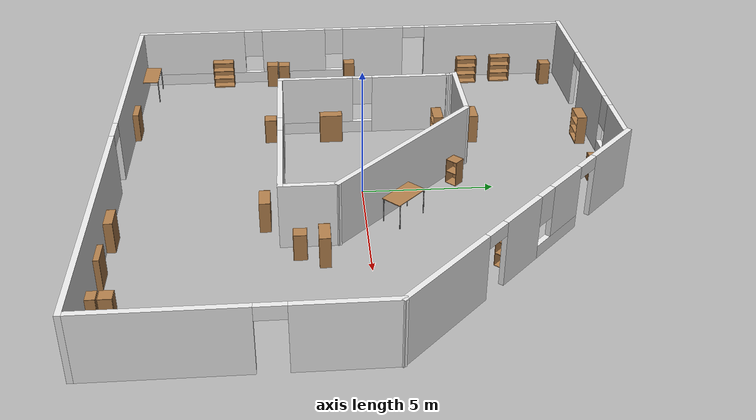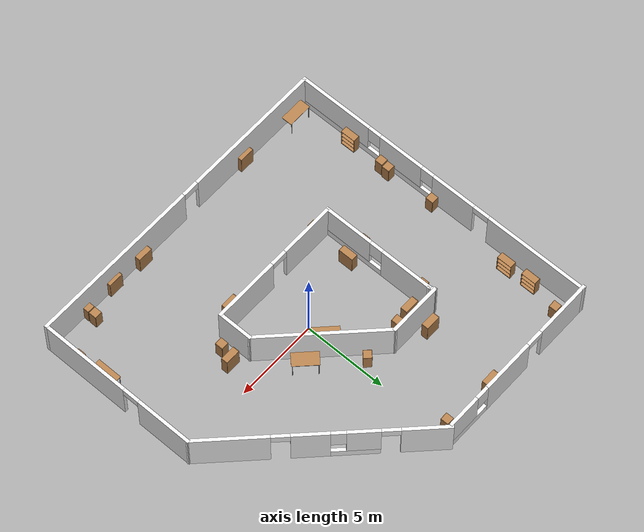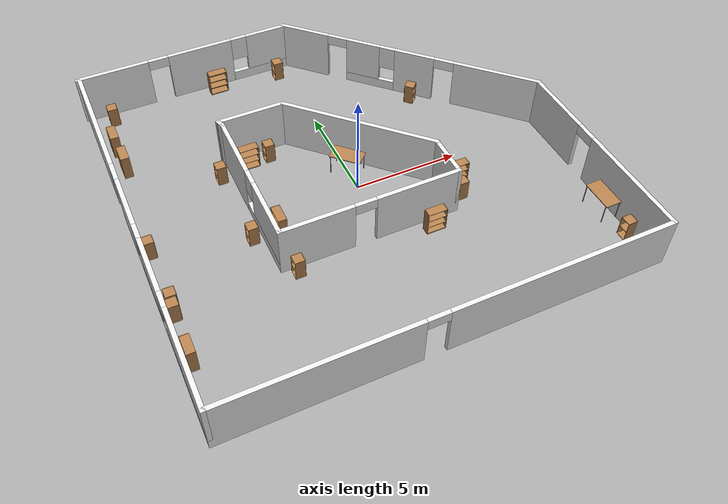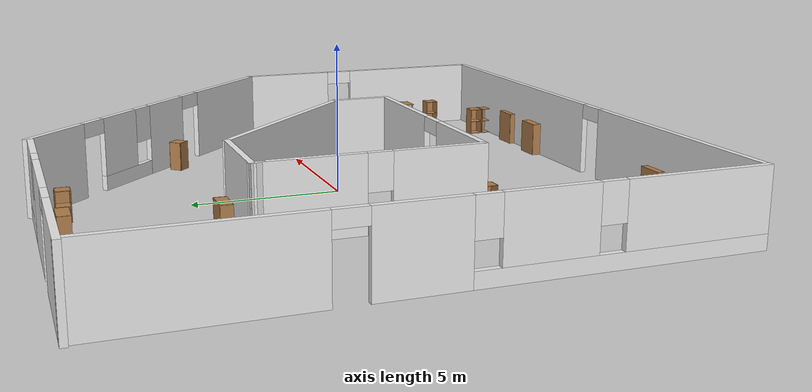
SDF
<sdf version="1.4">
 <world name="prepare">
  <model name="prepare">
   <link name="Wall_1">
    <pose>-4.94307 9.79265 0 0 -0 0</pose>
    <visual name="Wall_1_Visual_0">
     <pose>-3.52838 0 1.25 0 -0 0</pose>
     <geometry><box><size>3.5302 0.2 2.5</size></box></geometry>
     <material>
      <script><uri>file://media/materials/scripts/gazebo.material</uri><name>Gazebo/White</name></script>
     </material>
    </visual>
    <collision name="Wall_1_Collision_0">
     <geometry><box><size>3.5302 0.2 2.5</size></box></geometry>
     <pose>-3.52838 0 1.25 0 -0 0</pose>
    </collision>
    <visual name="Wall_1_Visual_1">
     <pose>0.845398 0 1.25 0 -0 0</pose>
     <geometry><box><size>3.21735 0.2 2.5</size></box></geometry>
     <material>
      <script><uri>file://media/materials/scripts/gazebo.material</uri><name>Gazebo/White</name></script>
     </material>
    </visual>
    <collision name="Wall_1_Collision_1">
     <geometry><box><size>3.21735 0.2 2.5</size></box></geometry>
     <pose>0.845398 0 1.25 0 -0 0</pose>
    </collision>
    <visual name="Wall_1_Visual_2">
     <pose>3.87378 0 0.25 0 -0 0</pose>
     <geometry><box><size>2.83941 0.2 0.5</size></box></geometry>
     <material>
      <script><uri>file://media/materials/scripts/gazebo.material</uri><name>Gazebo/White</name></script>
     </material>
    </visual>
    <collision name="Wall_1_Collision_2">
     <geometry><box><size>2.83941 0.2 0.5</size></box></geometry>
     <pose>3.87378 0 0.25 0 -0 0</pose>
    </collision>
    <visual name="Wall_1_Visual_3">
     <pose>4.27378 0 1.5 0 -0 0</pose>
     <geometry><box><size>2.0394 0.2 2</size></box></geometry>
     <material>
      <script><uri>file://media/materials/scripts/gazebo.material</uri><name>Gazebo/White</name></script>
     </material>
    </visual>
    <collision name="Wall_1_Collision_3">
     <geometry><box><size>2.0394 0.2 2</size></box></geometry>
     <pose>4.27378 0 1.5 0 -0 0</pose>
    </collision>
    <visual name="Wall_1_Visual_4">
     <pose>2.85407 0 1.9 0 -0 0</pose>
     <geometry><box><size>0.8 0.2 1.2</size></box></geometry>
     <material>
      <script><uri>file://media/materials/scripts/gazebo.material</uri><name>Gazebo/White</name></script>
     </material>
    </visual>
    <collision name="Wall_1_Collision_4">
     <geometry><box><size>0.8 0.2 1.2</size></box></geometry>
     <pose>2.85407 0 1.9 0 -0 0</pose>
    </collision>
    <visual name="Wall_1_Visual_5">
     <pose>-1.26328 0 2.25 0 -0 0</pose>
     <geometry><box><size>1 0.2 0.5</size></box></geometry>
     <material>
      <script><uri>file://media/materials/scripts/gazebo.material</uri><name>Gazebo/White</name></script>
     </material>
    </visual>
    <collision name="Wall_1_Collision_5">
     <geometry><box><size>1 0.2 0.5</size></box></geometry>
     <pose>-1.26328 0 2.25 0 -0 0</pose>
    </collision>
    <velocity_decay><linear>0</linear><angular>0</angular></velocity_decay>
   </link>
   <link name="Wall_10">
    <collision name="Wall_10_Collision">
     <geometry><box><size>2.1651 0.2 2.5</size></box></geometry>
     <pose>0 0 1.25 0 -0 0</pose>
    </collision>
    <visual name="Wall_10_Visual">
     <pose>0 0 1.25 0 -0 0</pose>
     <geometry><box><size>2.1651 0.2 2.5</size></box></geometry>
     <material>
      <script><uri>file://media/materials/scripts/gazebo.material</uri><name>Gazebo/White</name></script>
     </material>
    </visual>
    <velocity_decay><linear>0</linear><angular>0</angular></velocity_decay>
    <pose>3.33843 -2.04474 0 0 -0 1.5708</pose>
   </link>
   <link name="Wall_11">
    <collision name="Wall_11_Collision">
     <geometry><box><size>7.61086 0.2 2.5</size></box></geometry>
     <pose>0 0 1.25 0 -0 0</pose>
    </collision>
    <visual name="Wall_11_Visual">
     <pose>0 0 1.25 0 -0 0</pose>
     <geometry><box><size>7.61086 0.2 2.5</size></box></geometry>
     <material>
      <script><uri>file://media/materials/scripts/gazebo.material</uri><name>Gazebo/White</name></script>
     </material>
    </visual>
    <velocity_decay><linear>0</linear><angular>0</angular></velocity_decay>
    <pose>0.718295 1.55795 0 0 -0 2.35619</pose>
   </link>
   <link name="Wall_12">
    <collision name="Wall_12_Collision">
     <geometry><box><size>3.28802 0.2 2.5</size></box></geometry>
     <pose>0 0 1.25 0 -0 0</pose>
    </collision>
    <visual name="Wall_12_Visual">
     <pose>0 0 1.25 0 -0 0</pose>
     <geometry><box><size>3.28802 0.2 2.5</size></box></geometry>
     <material>
      <script><uri>file://media/materials/scripts/gazebo.material</uri><name>Gazebo/White</name></script>
     </material>
    </visual>
    <velocity_decay><linear>0</linear><angular>0</angular></velocity_decay>
    <pose>-3.44585 4.17808 0 0 -0 3.14159</pose>
   </link>
   <link name="Wall_13">
    <collision name="Wall_13_Collision">
     <geometry><box><size>0.495914 0.2 2.5</size></box></geometry>
     <pose>0 0 1.25 0 -0 0</pose>
    </collision>
    <visual name="Wall_13_Visual">
     <pose>0 0 1.25 0 -0 0</pose>
     <geometry><box><size>0.495914 0.2 2.5</size></box></geometry>
     <material>
      <script><uri>file://media/materials/scripts/gazebo.material</uri><name>Gazebo/White</name></script>
     </material>
    </visual>
    <velocity_decay><linear>0</linear><angular>0</angular></velocity_decay>
    <pose>-4.94307 4.03772 0 0 0 -1.24905</pose>
   </link>
   <link name="Wall_3">
    <pose>-10.043 0.294669 0 0 0 -1.5708</pose>
    <visual name="Wall_3_Visual_0">
     <pose>-6.42924 0 1.25 0 -0 0</pose>
     <geometry><box><size>6.33749 0.2 2.5</size></box></geometry>
     <material>
      <script><uri>file://media/materials/scripts/gazebo.material</uri><name>Gazebo/White</name></script>
     </material>
    </visual>
    <collision name="Wall_3_Collision_0">
     <geometry><box><size>6.33749 0.2 2.5</size></box></geometry>
     <pose>-6.42924 0 1.25 0 -0 0</pose>
    </collision>
    <visual name="Wall_3_Visual_1">
     <pose>-0.885762 0 1.25 0 -0 0</pose>
     <geometry><box><size>2.74947 0.2 2.5</size></box></geometry>
     <material>
      <script><uri>file://media/materials/scripts/gazebo.material</uri><name>Gazebo/White</name></script>
     </material>
    </visual>
    <collision name="Wall_3_Collision_1">
     <geometry><box><size>2.74947 0.2 2.5</size></box></geometry>
     <pose>-0.885762 0 1.25 0 -0 0</pose>
    </collision>
    <visual name="Wall_3_Visual_2">
     <pose>5.04348 0 0.25 0 -0 0</pose>
     <geometry><box><size>9.10901 0.2 0.5</size></box></geometry>
     <material>
      <script><uri>file://media/materials/scripts/gazebo.material</uri><name>Gazebo/White</name></script>
     </material>
    </visual>
    <collision name="Wall_3_Collision_2">
     <geometry><box><size>9.10901 0.2 0.5</size></box></geometry>
     <pose>5.04348 0 0.25 0 -0 0</pose>
    </collision>
    <visual name="Wall_3_Visual_3">
     <pose>2.71371 0 1.5 0 -0 0</pose>
     <geometry><box><size>2.84947 0.2 2</size></box></geometry>
     <material>
      <script><uri>file://media/materials/scripts/gazebo.material</uri><name>Gazebo/White</name></script>
     </material>
    </visual>
    <collision name="Wall_3_Collision_3">
     <geometry><box><size>2.84947 0.2 2</size></box></geometry>
     <pose>2.71371 0 1.5 0 -0 0</pose>
    </collision>
    <visual name="Wall_3_Visual_4">
     <pose>7.26822 0 1.5 0 -0 0</pose>
     <geometry><box><size>4.65954 0.2 2</size></box></geometry>
     <material>
      <script><uri>file://media/materials/scripts/gazebo.material</uri><name>Gazebo/White</name></script>
     </material>
    </visual>
    <collision name="Wall_3_Collision_4">
     <geometry><box><size>4.65954 0.2 2</size></box></geometry>
     <pose>7.26822 0 1.5 0 -0 0</pose>
    </collision>
    <visual name="Wall_3_Visual_5">
     <pose>0.888974 0 1.9 0 -0 0</pose>
     <geometry><box><size>0.8 0.2 1.2</size></box></geometry>
     <material>
      <script><uri>file://media/materials/scripts/gazebo.material</uri><name>Gazebo/White</name></script>
     </material>
    </visual>
    <collision name="Wall_3_Collision_5">
     <geometry><box><size>0.8 0.2 1.2</size></box></geometry>
     <pose>0.888974 0 1.9 0 -0 0</pose>
    </collision>
    <visual name="Wall_3_Visual_6">
     <pose>4.53845 0 1.9 0 -0 0</pose>
     <geometry><box><size>0.8 0.2 1.2</size></box></geometry>
     <material>
      <script><uri>file://media/materials/scripts/gazebo.material</uri><name>Gazebo/White</name></script>
     </material>
    </visual>
    <collision name="Wall_3_Collision_6">
     <geometry><box><size>0.8 0.2 1.2</size></box></geometry>
     <pose>4.53845 0 1.9 0 -0 0</pose>
    </collision>
    <visual name="Wall_3_Visual_7">
     <pose>-2.7605 0 2.25 0 -0 0</pose>
     <geometry><box><size>1 0.2 0.5</size></box></geometry>
     <material>
      <script><uri>file://media/materials/scripts/gazebo.material</uri><name>Gazebo/White</name></script>
     </material>
    </visual>
    <collision name="Wall_3_Collision_7">
     <geometry><box><size>1 0.2 0.5</size></box></geometry>
     <pose>-2.7605 0 2.25 0 -0 0</pose>
    </collision>
    <velocity_decay><linear>0</linear><angular>0</angular></velocity_decay>
   </link>
   <link name="Wall_4">
    <pose>-0.170679 -9.20332 0 0 -0 0</pose>
    <visual name="Wall_4_Visual_0">
     <pose>-5.68063 0 1.25 0 -0 0</pose>
     <geometry><box><size>8.58332 0.2 2.5</size></box></geometry>
     <material>
      <script><uri>file://media/materials/scripts/gazebo.material</uri><name>Gazebo/White</name></script>
     </material>
    </visual>
    <collision name="Wall_4_Collision_0">
     <geometry><box><size>8.58332 0.2 2.5</size></box></geometry>
     <pose>-5.68063 0 1.25 0 -0 0</pose>
    </collision>
    <visual name="Wall_4_Visual_1">
     <pose>4.79166 0 1.25 0 -0 0</pose>
     <geometry><box><size>10.3613 0.2 2.5</size></box></geometry>
     <material>
      <script><uri>file://media/materials/scripts/gazebo.material</uri><name>Gazebo/White</name></script>
     </material>
    </visual>
    <collision name="Wall_4_Collision_1">
     <geometry><box><size>10.3613 0.2 2.5</size></box></geometry>
     <pose>4.79166 0 1.25 0 -0 0</pose>
    </collision>
    <visual name="Wall_4_Visual_2">
     <pose>-0.888974 0 2.25 0 -0 0</pose>
     <geometry><box><size>1 0.2 0.5</size></box></geometry>
     <material>
      <script><uri>file://media/materials/scripts/gazebo.material</uri><name>Gazebo/White</name></script>
     </material>
    </visual>
    <collision name="Wall_4_Collision_2">
     <geometry><box><size>1 0.2 0.5</size></box></geometry>
     <pose>-0.888974 0 2.25 0 -0 0</pose>
    </collision>
    <velocity_decay><linear>0</linear><angular>0</angular></velocity_decay>
   </link>
   <link name="Wall_5">
    <pose>9.70161 -4.33735 0 0 -0 1.5708</pose>
    <visual name="Wall_5_Visual_0">
     <pose>-2.21831 0 1.25 0 -0 0</pose>
     <geometry><box><size>5.4953 0.2 2.5</size></box></geometry>
     <material>
      <script><uri>file://media/materials/scripts/gazebo.material</uri><name>Gazebo/White</name></script>
     </material>
    </visual>
    <collision name="Wall_5_Collision_0">
     <geometry><box><size>5.4953 0.2 2.5</size></box></geometry>
     <pose>-2.21831 0 1.25 0 -0 0</pose>
    </collision>
    <visual name="Wall_5_Visual_1">
     <pose>3.24765 0 1.25 0 -0 0</pose>
     <geometry><box><size>3.43662 0.2 2.5</size></box></geometry>
     <material>
      <script><uri>file://media/materials/scripts/gazebo.material</uri><name>Gazebo/White</name></script>
     </material>
    </visual>
    <collision name="Wall_5_Collision_1">
     <geometry><box><size>3.43662 0.2 2.5</size></box></geometry>
     <pose>3.24765 0 1.25 0 -0 0</pose>
    </collision>
    <visual name="Wall_5_Visual_2">
     <pose>1.02934 0 2.25 0 -0 0</pose>
     <geometry><box><size>1 0.2 0.5</size></box></geometry>
     <material>
      <script><uri>file://media/materials/scripts/gazebo.material</uri><name>Gazebo/White</name></script>
     </material>
    </visual>
    <collision name="Wall_5_Collision_2">
     <geometry><box><size>1 0.2 0.5</size></box></geometry>
     <pose>1.02934 0 2.25 0 -0 0</pose>
    </collision>
    <velocity_decay><linear>0</linear><angular>0</angular></velocity_decay>
   </link>
   <link name="Wall_6">
    <pose>5.0228 5.20742 0 0 -0 2.35619</pose>
    <visual name="Wall_6_Visual_0">
     <pose>-4.60094 0 1.25 0 -0 0</pose>
     <geometry><box><size>4.23179 0.2 2.5</size></box></geometry>
     <material>
      <script><uri>file://media/materials/scripts/gazebo.material</uri><name>Gazebo/White</name></script>
     </material>
    </visual>
    <collision name="Wall_6_Collision_0">
     <geometry><box><size>4.23179 0.2 2.5</size></box></geometry>
     <pose>-4.60094 0 1.25 0 -0 0</pose>
    </collision>
    <visual name="Wall_6_Visual_1">
     <pose>-0.479347 0 1.25 0 -0 0</pose>
     <geometry><box><size>2.01141 0.2 2.5</size></box></geometry>
     <material>
      <script><uri>file://media/materials/scripts/gazebo.material</uri><name>Gazebo/White</name></script>
     </material>
    </visual>
    <collision name="Wall_6_Collision_1">
     <geometry><box><size>2.01141 0.2 2.5</size></box></geometry>
     <pose>-0.479347 0 1.25 0 -0 0</pose>
    </collision>
    <visual name="Wall_6_Visual_2">
     <pose>5.39497 0 1.25 0 -0 0</pose>
     <geometry><box><size>2.64375 0.2 2.5</size></box></geometry>
     <material>
      <script><uri>file://media/materials/scripts/gazebo.material</uri><name>Gazebo/White</name></script>
     </material>
    </visual>
    <collision name="Wall_6_Collision_2">
     <geometry><box><size>2.64375 0.2 2.5</size></box></geometry>
     <pose>5.39497 0 1.25 0 -0 0</pose>
    </collision>
    <visual name="Wall_6_Visual_3">
     <pose>1.79973 0 0.25 0 -0 0</pose>
     <geometry><box><size>2.54673 0.2 0.5</size></box></geometry>
     <material>
      <script><uri>file://media/materials/scripts/gazebo.material</uri><name>Gazebo/White</name></script>
     </material>
    </visual>
    <collision name="Wall_6_Collision_3">
     <geometry><box><size>2.54673 0.2 0.5</size></box></geometry>
     <pose>1.79973 0 0.25 0 -0 0</pose>
    </collision>
    <visual name="Wall_6_Visual_4">
     <pose>2.19972 0 1.5 0 -0 0</pose>
     <geometry><box><size>1.74673 0.2 2</size></box></geometry>
     <material>
      <script><uri>file://media/materials/scripts/gazebo.material</uri><name>Gazebo/White</name></script>
     </material>
    </visual>
    <collision name="Wall_6_Collision_4">
     <geometry><box><size>1.74673 0.2 2</size></box></geometry>
     <pose>2.19972 0 1.5 0 -0 0</pose>
    </collision>
    <visual name="Wall_6_Visual_5">
     <pose>0.926357 0 1.9 0 -0 0</pose>
     <geometry><box><size>0.8 0.2 1.2</size></box></geometry>
     <material>
      <script><uri>file://media/materials/scripts/gazebo.material</uri><name>Gazebo/White</name></script>
     </material>
    </visual>
    <collision name="Wall_6_Collision_5">
     <geometry><box><size>0.8 0.2 1.2</size></box></geometry>
     <pose>0.926357 0 1.9 0 -0 0</pose>
    </collision>
    <visual name="Wall_6_Visual_6">
     <pose>-1.98505 0 2.25 0 -0 0</pose>
     <geometry><box><size>1 0.2 0.5</size></box></geometry>
     <material>
      <script><uri>file://media/materials/scripts/gazebo.material</uri><name>Gazebo/White</name></script>
     </material>
    </visual>
    <collision name="Wall_6_Collision_6">
     <geometry><box><size>1 0.2 0.5</size></box></geometry>
     <pose>-1.98505 0 2.25 0 -0 0</pose>
    </collision>
    <visual name="Wall_6_Visual_7">
     <pose>3.57309 0 2.25 0 -0 0</pose>
     <geometry><box><size>1 0.2 0.5</size></box></geometry>
     <material>
      <script><uri>file://media/materials/scripts/gazebo.material</uri><name>Gazebo/White</name></script>
     </material>
    </visual>
    <collision name="Wall_6_Collision_7">
     <geometry><box><size>1 0.2 0.5</size></box></geometry>
     <pose>3.57309 0 2.25 0 -0 0</pose>
    </collision>
    <velocity_decay><linear>0</linear><angular>0</angular></velocity_decay>
   </link>
   <link name="Wall_8">
    <pose>-4.89628 0.435033 0 0 0 -1.5708</pose>
    <visual name="Wall_8_Visual_0">
     <pose>-1.93437 0 1.25 0 -0 0</pose>
     <geometry><box><size>3.2559 0.2 2.5</size></box></geometry>
     <material>
      <script><uri>file://media/materials/scripts/gazebo.material</uri><name>Gazebo/White</name></script>
     </material>
    </visual>
    <collision name="Wall_8_Collision_0">
     <geometry><box><size>3.2559 0.2 2.5</size></box></geometry>
     <pose>-1.93437 0 1.25 0 -0 0</pose>
    </collision>
    <visual name="Wall_8_Visual_1">
     <pose>1.62795 0 0.25 0 -0 0</pose>
     <geometry><box><size>3.86874 0.2 0.5</size></box></geometry>
     <material>
      <script><uri>file://media/materials/scripts/gazebo.material</uri><name>Gazebo/White</name></script>
     </material>
    </visual>
    <collision name="Wall_8_Collision_1">
     <geometry><box><size>3.86874 0.2 0.5</size></box></geometry>
     <pose>1.62795 0 0.25 0 -0 0</pose>
    </collision>
    <visual name="Wall_8_Visual_2">
     <pose>2.02795 0 1.5 0 -0 0</pose>
     <geometry><box><size>3.06874 0.2 2</size></box></geometry>
     <material>
      <script><uri>file://media/materials/scripts/gazebo.material</uri><name>Gazebo/White</name></script>
     </material>
    </visual>
    <collision name="Wall_8_Collision_2">
     <geometry><box><size>3.06874 0.2 2</size></box></geometry>
     <pose>2.02795 0 1.5 0 -0 0</pose>
    </collision>
    <visual name="Wall_8_Visual_3">
     <pose>0.093576 0 1.9 0 -0 0</pose>
     <geometry><box><size>0.8 0.2 1.2</size></box></geometry>
     <material>
      <script><uri>file://media/materials/scripts/gazebo.material</uri><name>Gazebo/White</name></script>
     </material>
    </visual>
    <collision name="Wall_8_Collision_3">
     <geometry><box><size>0.8 0.2 1.2</size></box></geometry>
     <pose>0.093576 0 1.9 0 -0 0</pose>
    </collision>
    <velocity_decay><linear>0</linear><angular>0</angular></velocity_decay>
   </link>
   <link name="Wall_9">
    <pose>-0.778925 -3.02729 0 0 -0 0</pose>
    <visual name="Wall_9_Visual_0">
     <pose>-2.49904 0 1.25 0 -0 0</pose>
     <geometry><box><size>3.43662 0.2 2.5</size></box></geometry>
     <material>
      <script><uri>file://media/materials/scripts/gazebo.material</uri><name>Gazebo/White</name></script>
     </material>
    </visual>
    <collision name="Wall_9_Collision_0">
     <geometry><box><size>3.43662 0.2 2.5</size></box></geometry>
     <pose>-2.49904 0 1.25 0 -0 0</pose>
    </collision>
    <visual name="Wall_9_Visual_1">
     <pose>2.21831 0 1.25 0 -0 0</pose>
     <geometry><box><size>3.99808 0.2 2.5</size></box></geometry>
     <material>
      <script><uri>file://media/materials/scripts/gazebo.material</uri><name>Gazebo/White</name></script>
     </material>
    </visual>
    <collision name="Wall_9_Collision_1">
     <geometry><box><size>3.99808 0.2 2.5</size></box></geometry>
     <pose>2.21831 0 1.25 0 -0 0</pose>
    </collision>
    <visual name="Wall_9_Visual_2">
     <pose>-0.280729 0 2.25 0 -0 0</pose>
     <geometry><box><size>1 0.2 0.5</size></box></geometry>
     <material>
      <script><uri>file://media/materials/scripts/gazebo.material</uri><name>Gazebo/White</name></script>
     </material>
    </visual>
    <collision name="Wall_9_Collision_2">
     <geometry><box><size>1 0.2 0.5</size></box></geometry>
     <pose>-0.280729 0 2.25 0 -0 0</pose>
    </collision>
    <velocity_decay><linear>0</linear><angular>0</angular></velocity_decay>
   </link>
   <static>1</static>
  </model>
  <physics type="ode">
   <max_step_size>0.001</max_step_size>
   <real_time_factor>1</real_time_factor>
   <real_time_update_rate>1000</real_time_update_rate>
   <gravity>0 0 -9.8</gravity>
  </physics>
  <scene><ambient>0.4 0.4 0.4 1</ambient><background>0.7 0.7 0.7 1</background><shadows>1</shadows></scene>
  <audio><device>default</device></audio>
  <spherical_coordinates>
   <surface_model>EARTH_WGS84</surface_model>
   <latitude_deg>0</latitude_deg>
   <longitude_deg>0</longitude_deg>
   <elevation>0</elevation>
   <heading_deg>0</heading_deg>
  </spherical_coordinates>
  <model name="bookshelf">
   <static>1</static>
   <link name="link">
    <inertial><mass>1</mass></inertial>
    <collision name="back">
     <pose>0 0.005 0.6 0 -0 0</pose>
     <geometry><box><size>0.9 0.01 1.2</size></box></geometry>
    </collision>
    <visual name="visual1">
     <pose>0 0.005 0.6 0 -0 0</pose>
     <geometry><box><size>0.9 0.01 1.2</size></box></geometry>
     <material>
      <script><uri>file://media/materials/scripts/gazebo.material</uri><name>Gazebo/Wood</name></script>
     </material>
    </visual>
    <collision name="left_side">
     <pose>0.45 -0.195 0.6 0 -0 0</pose>
     <geometry><box><size>0.02 0.4 1.2</size></box></geometry>
    </collision>
    <visual name="visual2">
     <pose>0.45 -0.195 0.6 0 -0 0</pose>
     <geometry><box><size>0.02 0.4 1.2</size></box></geometry>
     <material>
      <script><uri>file://media/materials/scripts/gazebo.material</uri><name>Gazebo/Wood</name></script>
     </material>
    </visual>
    <collision name="right_side">
     <pose>-0.45 -0.195 0.6 0 -0 0</pose>
     <geometry><box><size>0.02 0.4 1.2</size></box></geometry>
    </collision>
    <visual name="visual3">
     <pose>-0.45 -0.195 0.6 0 -0 0</pose>
     <geometry><box><size>0.02 0.4 1.2</size></box></geometry>
     <material>
      <script><uri>file://media/materials/scripts/gazebo.material</uri><name>Gazebo/Wood</name></script>
     </material>
    </visual>
    <collision name="bottom">
     <pose>0 -0.195 0.03 0 -0 0</pose>
     <geometry><box><size>0.88 0.4 0.06</size></box></geometry>
    </collision>
    <visual name="visual4">
     <pose>0 -0.195 0.03 0 -0 0</pose>
     <geometry><box><size>0.88 0.4 0.06</size></box></geometry>
     <material>
      <script><uri>file://media/materials/scripts/gazebo.material</uri><name>Gazebo/Wood</name></script>
     </material>
    </visual>
    <collision name="top">
     <pose>0 -0.195 1.19 0 -0 0</pose>
     <geometry><box><size>0.88 0.4 0.02</size></box></geometry>
    </collision>
    <visual name="visual5">
     <pose>0 -0.195 1.19 0 -0 0</pose>
     <geometry><box><size>0.88 0.4 0.02</size></box></geometry>
     <material>
      <script><uri>file://media/materials/scripts/gazebo.material</uri><name>Gazebo/Wood</name></script>
     </material>
    </visual>
    <collision name="low_shelf">
     <pose>0 -0.195 0.43 0 -0 0</pose>
     <geometry><box><size>0.88 0.4 0.02</size></box></geometry>
    </collision>
    <visual name="visual6">
     <pose>0 -0.195 0.43 0 -0 0</pose>
     <geometry><box><size>0.88 0.4 0.02</size></box></geometry>
     <material>
      <script><uri>file://media/materials/scripts/gazebo.material</uri><name>Gazebo/Wood</name></script>
     </material>
    </visual>
    <collision name="high_shelf">
     <pose>0 -0.195 0.8 0 -0 0</pose>
     <geometry><box><size>0.88 0.4 0.02</size></box></geometry>
    </collision>
    <visual name="visual7">
     <pose>0 -0.195 0.8 0 -0 0</pose>
     <geometry><box><size>0.88 0.4 0.02</size></box></geometry>
     <material>
      <script><uri>file://media/materials/scripts/gazebo.material</uri><name>Gazebo/Wood</name></script>
     </material>
    </visual>
    <velocity_decay><linear>0</linear><angular>0</angular></velocity_decay>
   </link>
   <pose>-4 3.56665 0 0 -0 0</pose>
  </model>
  <model name="cabinet">
   <static>1</static>
   <link name="cabinet_bottom_plate">
    <inertial>
     <pose>0 0 -1 0 -0 0</pose>
     <inertia><ixx>2.05</ixx><ixy>0</ixy><ixz>0</ixz><iyy>2.05</iyy><iyz>0</iyz><izz>2.05</izz></inertia>
     <mass>25</mass>
    </inertial>
    <collision name="cabinet_bottom_plate_geom">
     <pose>0 0 0.01 0 -0 0</pose>
     <geometry><box><size>0.45 0.45 0.02</size></box></geometry>
    </collision>
    <visual name="cabinet_bottom_plate_geom_visual">
     <pose>0 0 0.01 0 -0 0</pose>
     <geometry><box><size>0.45 0.45 0.02</size></box></geometry>
     <material>
      <script><uri>file://media/materials/scripts/gazebo.material</uri><name>Gazebo/Wood</name></script>
     </material>
    </visual>
    <collision name="cabinet_bottom_plate_geom_cabinet_back_plate">
     <pose>0.235 0 0.51 0 -0 0</pose>
     <geometry><box><size>0.02 0.45 1.02</size></box></geometry>
    </collision>
    <visual name="cabinet_bottom_plate_geom_cabinet_back_plate_visual">
     <pose>0.235 0 0.51 0 -0 0</pose>
     <geometry><box><size>0.02 0.45 1.02</size></box></geometry>
     <material>
      <script><uri>file://media/materials/scripts/gazebo.material</uri><name>Gazebo/Wood</name></script>
     </material>
    </visual>
    <collision name="cabinet_bottom_plate_geom_cabinet_left_plate">
     <pose>0 0.235 0.51 0 -0 0</pose>
     <geometry><box><size>0.45 0.02 1.02</size></box></geometry>
    </collision>
    <visual name="cabinet_bottom_plate_geom_cabinet_left_plate_visual">
     <pose>0 0.235 0.51 0 -0 0</pose>
     <geometry><box><size>0.45 0.02 1.02</size></box></geometry>
     <material>
      <script><uri>file://media/materials/scripts/gazebo.material</uri><name>Gazebo/Wood</name></script>
     </material>
    </visual>
    <collision name="cabinet_bottom_plate_geom_cabinet_middle_plate">
     <pose>0 0 0.51 0 -0 0</pose>
     <geometry><box><size>0.45 0.45 0.02</size></box></geometry>
    </collision>
    <visual name="cabinet_bottom_plate_geom_cabinet_middle_plate_visual">
     <pose>0 0 0.51 0 -0 0</pose>
     <geometry><box><size>0.45 0.45 0.02</size></box></geometry>
     <material>
      <script><uri>file://media/materials/scripts/gazebo.material</uri><name>Gazebo/Wood</name></script>
     </material>
    </visual>
    <collision name="cabinet_bottom_plate_geom_cabinet_right_plate">
     <pose>0 -0.235 0.51 0 -0 0</pose>
     <geometry><box><size>0.45 0.02 1.02</size></box></geometry>
    </collision>
    <visual name="cabinet_bottom_plate_geom_cabinet_right_plate_visual">
     <pose>0 -0.235 0.51 0 -0 0</pose>
     <geometry><box><size>0.45 0.02 1.02</size></box></geometry>
     <material>
      <script><uri>file://media/materials/scripts/gazebo.material</uri><name>Gazebo/Wood</name></script>
     </material>
    </visual>
    <collision name="cabinet_bottom_plate_geom_cabinet_top_plate">
     <pose>0 0 1.01 0 -0 0</pose>
     <geometry><box><size>0.45 0.45 0.02</size></box></geometry>
    </collision>
    <visual name="cabinet_bottom_plate_geom_cabinet_top_plate_visual">
     <pose>0 0 1.01 0 -0 0</pose>
     <geometry><box><size>0.45 0.45 0.02</size></box></geometry>
     <material>
      <script><uri>file://media/materials/scripts/gazebo.material</uri><name>Gazebo/Wood</name></script>
     </material>
    </visual>
    <velocity_decay><linear>0</linear><angular>0</angular></velocity_decay>
   </link>
   <pose>-4.33134 -3.46856 0 0 -0 0</pose>
  </model>
  <model name="bookshelf_0">
   <static>1</static>
   <link name="link">
    <inertial><mass>1</mass></inertial>
    <collision name="back">
     <pose>0 0.005 0.6 0 -0 0</pose>
     <geometry><box><size>0.9 0.01 1.2</size></box></geometry>
    </collision>
    <visual name="visual1">
     <pose>0 0.005 0.6 0 -0 0</pose>
     <geometry><box><size>0.9 0.01 1.2</size></box></geometry>
     <material>
      <script><uri>file://media/materials/scripts/gazebo.material</uri><name>Gazebo/Wood</name></script>
     </material>
    </visual>
    <collision name="left_side">
     <pose>0.45 -0.195 0.6 0 -0 0</pose>
     <geometry><box><size>0.02 0.4 1.2</size></box></geometry>
    </collision>
    <visual name="visual2">
     <pose>0.45 -0.195 0.6 0 -0 0</pose>
     <geometry><box><size>0.02 0.4 1.2</size></box></geometry>
     <material>
      <script><uri>file://media/materials/scripts/gazebo.material</uri><name>Gazebo/Wood</name></script>
     </material>
    </visual>
    <collision name="right_side">
     <pose>-0.45 -0.195 0.6 0 -0 0</pose>
     <geometry><box><size>0.02 0.4 1.2</size></box></geometry>
    </collision>
    <visual name="visual3">
     <pose>-0.45 -0.195 0.6 0 -0 0</pose>
     <geometry><box><size>0.02 0.4 1.2</size></box></geometry>
     <material>
      <script><uri>file://media/materials/scripts/gazebo.material</uri><name>Gazebo/Wood</name></script>
     </material>
    </visual>
    <collision name="bottom">
     <pose>0 -0.195 0.03 0 -0 0</pose>
     <geometry><box><size>0.88 0.4 0.06</size></box></geometry>
    </collision>
    <visual name="visual4">
     <pose>0 -0.195 0.03 0 -0 0</pose>
     <geometry><box><size>0.88 0.4 0.06</size></box></geometry>
     <material>
      <script><uri>file://media/materials/scripts/gazebo.material</uri><name>Gazebo/Wood</name></script>
     </material>
    </visual>
    <collision name="top">
     <pose>0 -0.195 1.19 0 -0 0</pose>
     <geometry><box><size>0.88 0.4 0.02</size></box></geometry>
    </collision>
    <visual name="visual5">
     <pose>0 -0.195 1.19 0 -0 0</pose>
     <geometry><box><size>0.88 0.4 0.02</size></box></geometry>
     <material>
      <script><uri>file://media/materials/scripts/gazebo.material</uri><name>Gazebo/Wood</name></script>
     </material>
    </visual>
    <collision name="low_shelf">
     <pose>0 -0.195 0.43 0 -0 0</pose>
     <geometry><box><size>0.88 0.4 0.02</size></box></geometry>
    </collision>
    <visual name="visual6">
     <pose>0 -0.195 0.43 0 -0 0</pose>
     <geometry><box><size>0.88 0.4 0.02</size></box></geometry>
     <material>
      <script><uri>file://media/materials/scripts/gazebo.material</uri><name>Gazebo/Wood</name></script>
     </material>
    </visual>
    <collision name="high_shelf">
     <pose>0 -0.195 0.8 0 -0 0</pose>
     <geometry><box><size>0.88 0.4 0.02</size></box></geometry>
    </collision>
    <visual name="visual7">
     <pose>0 -0.195 0.8 0 -0 0</pose>
     <geometry><box><size>0.88 0.4 0.02</size></box></geometry>
     <material>
      <script><uri>file://media/materials/scripts/gazebo.material</uri><name>Gazebo/Wood</name></script>
     </material>
    </visual>
    <velocity_decay><linear>0</linear><angular>0</angular></velocity_decay>
   </link>
   <pose>-4 -1 0 0 0 -1.5708</pose>
  </model>
  <model name="cabinet_0">
   <static>1</static>
   <link name="cabinet_bottom_plate">
    <inertial>
     <pose>0 0 -1 0 -0 0</pose>
     <inertia><ixx>2.05</ixx><ixy>0</ixy><ixz>0</ixz><iyy>2.05</iyy><iyz>0</iyz><izz>2.05</izz></inertia>
     <mass>25</mass>
    </inertial>
    <collision name="cabinet_bottom_plate_geom">
     <pose>0 0 0.01 0 -0 0</pose>
     <geometry><box><size>0.45 0.45 0.02</size></box></geometry>
    </collision>
    <visual name="cabinet_bottom_plate_geom_visual">
     <pose>0 0 0.01 0 -0 0</pose>
     <geometry><box><size>0.45 0.45 0.02</size></box></geometry>
     <material>
      <script><uri>file://media/materials/scripts/gazebo.material</uri><name>Gazebo/Wood</name></script>
     </material>
    </visual>
    <collision name="cabinet_bottom_plate_geom_cabinet_back_plate">
     <pose>0.235 0 0.51 0 -0 0</pose>
     <geometry><box><size>0.02 0.45 1.02</size></box></geometry>
    </collision>
    <visual name="cabinet_bottom_plate_geom_cabinet_back_plate_visual">
     <pose>0.235 0 0.51 0 -0 0</pose>
     <geometry><box><size>0.02 0.45 1.02</size></box></geometry>
     <material>
      <script><uri>file://media/materials/scripts/gazebo.material</uri><name>Gazebo/Wood</name></script>
     </material>
    </visual>
    <collision name="cabinet_bottom_plate_geom_cabinet_left_plate">
     <pose>0 0.235 0.51 0 -0 0</pose>
     <geometry><box><size>0.45 0.02 1.02</size></box></geometry>
    </collision>
    <visual name="cabinet_bottom_plate_geom_cabinet_left_plate_visual">
     <pose>0 0.235 0.51 0 -0 0</pose>
     <geometry><box><size>0.45 0.02 1.02</size></box></geometry>
     <material>
      <script><uri>file://media/materials/scripts/gazebo.material</uri><name>Gazebo/Wood</name></script>
     </material>
    </visual>
    <collision name="cabinet_bottom_plate_geom_cabinet_middle_plate">
     <pose>0 0 0.51 0 -0 0</pose>
     <geometry><box><size>0.45 0.45 0.02</size></box></geometry>
    </collision>
    <visual name="cabinet_bottom_plate_geom_cabinet_middle_plate_visual">
     <pose>0 0 0.51 0 -0 0</pose>
     <geometry><box><size>0.45 0.45 0.02</size></box></geometry>
     <material>
      <script><uri>file://media/materials/scripts/gazebo.material</uri><name>Gazebo/Wood</name></script>
     </material>
    </visual>
    <collision name="cabinet_bottom_plate_geom_cabinet_right_plate">
     <pose>0 -0.235 0.51 0 -0 0</pose>
     <geometry><box><size>0.45 0.02 1.02</size></box></geometry>
    </collision>
    <visual name="cabinet_bottom_plate_geom_cabinet_right_plate_visual">
     <pose>0 -0.235 0.51 0 -0 0</pose>
     <geometry><box><size>0.45 0.02 1.02</size></box></geometry>
     <material>
      <script><uri>file://media/materials/scripts/gazebo.material</uri><name>Gazebo/Wood</name></script>
     </material>
    </visual>
    <collision name="cabinet_bottom_plate_geom_cabinet_top_plate">
     <pose>0 0 1.01 0 -0 0</pose>
     <geometry><box><size>0.45 0.45 0.02</size></box></geometry>
    </collision>
    <visual name="cabinet_bottom_plate_geom_cabinet_top_plate_visual">
     <pose>0 0 1.01 0 -0 0</pose>
     <geometry><box><size>0.45 0.45 0.02</size></box></geometry>
     <material>
      <script><uri>file://media/materials/scripts/gazebo.material</uri><name>Gazebo/Wood</name></script>
     </material>
    </visual>
    <velocity_decay><linear>0</linear><angular>0</angular></velocity_decay>
   </link>
   <pose>5 4.45603 0 0 -0 2.3561</pose>
  </model>
  <model name="bookshelf_1">
   <static>1</static>
   <link name="link">
    <inertial><mass>1</mass></inertial>
    <collision name="back">
     <pose>0 0.005 0.6 0 -0 0</pose>
     <geometry><box><size>0.9 0.01 1.2</size></box></geometry>
    </collision>
    <visual name="visual1">
     <pose>0 0.005 0.6 0 -0 0</pose>
     <geometry><box><size>0.9 0.01 1.2</size></box></geometry>
     <material>
      <script><uri>file://media/materials/scripts/gazebo.material</uri><name>Gazebo/Wood</name></script>
     </material>
    </visual>
    <collision name="left_side">
     <pose>0.45 -0.195 0.6 0 -0 0</pose>
     <geometry><box><size>0.02 0.4 1.2</size></box></geometry>
    </collision>
    <visual name="visual2">
     <pose>0.45 -0.195 0.6 0 -0 0</pose>
     <geometry><box><size>0.02 0.4 1.2</size></box></geometry>
     <material>
      <script><uri>file://media/materials/scripts/gazebo.material</uri><name>Gazebo/Wood</name></script>
     </material>
    </visual>
    <collision name="right_side">
     <pose>-0.45 -0.195 0.6 0 -0 0</pose>
     <geometry><box><size>0.02 0.4 1.2</size></box></geometry>
    </collision>
    <visual name="visual3">
     <pose>-0.45 -0.195 0.6 0 -0 0</pose>
     <geometry><box><size>0.02 0.4 1.2</size></box></geometry>
     <material>
      <script><uri>file://media/materials/scripts/gazebo.material</uri><name>Gazebo/Wood</name></script>
     </material>
    </visual>
    <collision name="bottom">
     <pose>0 -0.195 0.03 0 -0 0</pose>
     <geometry><box><size>0.88 0.4 0.06</size></box></geometry>
    </collision>
    <visual name="visual4">
     <pose>0 -0.195 0.03 0 -0 0</pose>
     <geometry><box><size>0.88 0.4 0.06</size></box></geometry>
     <material>
      <script><uri>file://media/materials/scripts/gazebo.material</uri><name>Gazebo/Wood</name></script>
     </material>
    </visual>
    <collision name="top">
     <pose>0 -0.195 1.19 0 -0 0</pose>
     <geometry><box><size>0.88 0.4 0.02</size></box></geometry>
    </collision>
    <visual name="visual5">
     <pose>0 -0.195 1.19 0 -0 0</pose>
     <geometry><box><size>0.88 0.4 0.02</size></box></geometry>
     <material>
      <script><uri>file://media/materials/scripts/gazebo.material</uri><name>Gazebo/Wood</name></script>
     </material>
    </visual>
    <collision name="low_shelf">
     <pose>0 -0.195 0.43 0 -0 0</pose>
     <geometry><box><size>0.88 0.4 0.02</size></box></geometry>
    </collision>
    <visual name="visual6">
     <pose>0 -0.195 0.43 0 -0 0</pose>
     <geometry><box><size>0.88 0.4 0.02</size></box></geometry>
     <material>
      <script><uri>file://media/materials/scripts/gazebo.material</uri><name>Gazebo/Wood</name></script>
     </material>
    </visual>
    <collision name="high_shelf">
     <pose>0 -0.195 0.8 0 -0 0</pose>
     <geometry><box><size>0.88 0.4 0.02</size></box></geometry>
    </collision>
    <visual name="visual7">
     <pose>0 -0.195 0.8 0 -0 0</pose>
     <geometry><box><size>0.88 0.4 0.02</size></box></geometry>
     <material>
      <script><uri>file://media/materials/scripts/gazebo.material</uri><name>Gazebo/Wood</name></script>
     </material>
    </visual>
    <velocity_decay><linear>0</linear><angular>0</angular></velocity_decay>
   </link>
   <pose>-3.5501 9.41682 0 0 -0 0</pose>
  </model>
  <model name="cabinet_1">
   <static>1</static>
   <link name="cabinet_bottom_plate">
    <inertial>
     <pose>0 0 -1 0 -0 0</pose>
     <inertia><ixx>2.05</ixx><ixy>0</ixy><ixz>0</ixz><iyy>2.05</iyy><iyz>0</iyz><izz>2.05</izz></inertia>
     <mass>25</mass>
    </inertial>
    <collision name="cabinet_bottom_plate_geom">
     <pose>0 0 0.01 0 -0 0</pose>
     <geometry><box><size>0.45 0.45 0.02</size></box></geometry>
    </collision>
    <visual name="cabinet_bottom_plate_geom_visual">
     <pose>0 0 0.01 0 -0 0</pose>
     <geometry><box><size>0.45 0.45 0.02</size></box></geometry>
     <material>
      <script><uri>file://media/materials/scripts/gazebo.material</uri><name>Gazebo/Wood</name></script>
     </material>
    </visual>
    <collision name="cabinet_bottom_plate_geom_cabinet_back_plate">
     <pose>0.235 0 0.51 0 -0 0</pose>
     <geometry><box><size>0.02 0.45 1.02</size></box></geometry>
    </collision>
    <visual name="cabinet_bottom_plate_geom_cabinet_back_plate_visual">
     <pose>0.235 0 0.51 0 -0 0</pose>
     <geometry><box><size>0.02 0.45 1.02</size></box></geometry>
     <material>
      <script><uri>file://media/materials/scripts/gazebo.material</uri><name>Gazebo/Wood</name></script>
     </material>
    </visual>
    <collision name="cabinet_bottom_plate_geom_cabinet_left_plate">
     <pose>0 0.235 0.51 0 -0 0</pose>
     <geometry><box><size>0.45 0.02 1.02</size></box></geometry>
    </collision>
    <visual name="cabinet_bottom_plate_geom_cabinet_left_plate_visual">
     <pose>0 0.235 0.51 0 -0 0</pose>
     <geometry><box><size>0.45 0.02 1.02</size></box></geometry>
     <material>
      <script><uri>file://media/materials/scripts/gazebo.material</uri><name>Gazebo/Wood</name></script>
     </material>
    </visual>
    <collision name="cabinet_bottom_plate_geom_cabinet_middle_plate">
     <pose>0 0 0.51 0 -0 0</pose>
     <geometry><box><size>0.45 0.45 0.02</size></box></geometry>
    </collision>
    <visual name="cabinet_bottom_plate_geom_cabinet_middle_plate_visual">
     <pose>0 0 0.51 0 -0 0</pose>
     <geometry><box><size>0.45 0.45 0.02</size></box></geometry>
     <material>
      <script><uri>file://media/materials/scripts/gazebo.material</uri><name>Gazebo/Wood</name></script>
     </material>
    </visual>
    <collision name="cabinet_bottom_plate_geom_cabinet_right_plate">
     <pose>0 -0.235 0.51 0 -0 0</pose>
     <geometry><box><size>0.45 0.02 1.02</size></box></geometry>
    </collision>
    <visual name="cabinet_bottom_plate_geom_cabinet_right_plate_visual">
     <pose>0 -0.235 0.51 0 -0 0</pose>
     <geometry><box><size>0.45 0.02 1.02</size></box></geometry>
     <material>
      <script><uri>file://media/materials/scripts/gazebo.material</uri><name>Gazebo/Wood</name></script>
     </material>
    </visual>
    <collision name="cabinet_bottom_plate_geom_cabinet_top_plate">
     <pose>0 0 1.01 0 -0 0</pose>
     <geometry><box><size>0.45 0.45 0.02</size></box></geometry>
    </collision>
    <visual name="cabinet_bottom_plate_geom_cabinet_top_plate_visual">
     <pose>0 0 1.01 0 -0 0</pose>
     <geometry><box><size>0.45 0.45 0.02</size></box></geometry>
     <material>
      <script><uri>file://media/materials/scripts/gazebo.material</uri><name>Gazebo/Wood</name></script>
     </material>
    </visual>
    <velocity_decay><linear>0</linear><angular>0</angular></velocity_decay>
   </link>
   <pose>-0.400209 9 0 0 -0 0</pose>
  </model>
  <model name="cabinet_2">
   <static>1</static>
   <link name="cabinet_bottom_plate">
    <inertial>
     <pose>0 0 -1 0 -0 0</pose>
     <inertia><ixx>2.05</ixx><ixy>0</ixy><ixz>0</ixz><iyy>2.05</iyy><iyz>0</iyz><izz>2.05</izz></inertia>
     <mass>25</mass>
    </inertial>
    <collision name="cabinet_bottom_plate_geom">
     <pose>0 0 0.01 0 -0 0</pose>
     <geometry><box><size>0.45 0.45 0.02</size></box></geometry>
    </collision>
    <visual name="cabinet_bottom_plate_geom_visual">
     <pose>0 0 0.01 0 -0 0</pose>
     <geometry><box><size>0.45 0.45 0.02</size></box></geometry>
     <material>
      <script><uri>file://media/materials/scripts/gazebo.material</uri><name>Gazebo/Wood</name></script>
     </material>
    </visual>
    <collision name="cabinet_bottom_plate_geom_cabinet_back_plate">
     <pose>0.235 0 0.51 0 -0 0</pose>
     <geometry><box><size>0.02 0.45 1.02</size></box></geometry>
    </collision>
    <visual name="cabinet_bottom_plate_geom_cabinet_back_plate_visual">
     <pose>0.235 0 0.51 0 -0 0</pose>
     <geometry><box><size>0.02 0.45 1.02</size></box></geometry>
     <material>
      <script><uri>file://media/materials/scripts/gazebo.material</uri><name>Gazebo/Wood</name></script>
     </material>
    </visual>
    <collision name="cabinet_bottom_plate_geom_cabinet_left_plate">
     <pose>0 0.235 0.51 0 -0 0</pose>
     <geometry><box><size>0.45 0.02 1.02</size></box></geometry>
    </collision>
    <visual name="cabinet_bottom_plate_geom_cabinet_left_plate_visual">
     <pose>0 0.235 0.51 0 -0 0</pose>
     <geometry><box><size>0.45 0.02 1.02</size></box></geometry>
     <material>
      <script><uri>file://media/materials/scripts/gazebo.material</uri><name>Gazebo/Wood</name></script>
     </material>
    </visual>
    <collision name="cabinet_bottom_plate_geom_cabinet_middle_plate">
     <pose>0 0 0.51 0 -0 0</pose>
     <geometry><box><size>0.45 0.45 0.02</size></box></geometry>
    </collision>
    <visual name="cabinet_bottom_plate_geom_cabinet_middle_plate_visual">
     <pose>0 0 0.51 0 -0 0</pose>
     <geometry><box><size>0.45 0.45 0.02</size></box></geometry>
     <material>
      <script><uri>file://media/materials/scripts/gazebo.material</uri><name>Gazebo/Wood</name></script>
     </material>
    </visual>
    <collision name="cabinet_bottom_plate_geom_cabinet_right_plate">
     <pose>0 -0.235 0.51 0 -0 0</pose>
     <geometry><box><size>0.45 0.02 1.02</size></box></geometry>
    </collision>
    <visual name="cabinet_bottom_plate_geom_cabinet_right_plate_visual">
     <pose>0 -0.235 0.51 0 -0 0</pose>
     <geometry><box><size>0.45 0.02 1.02</size></box></geometry>
     <material>
      <script><uri>file://media/materials/scripts/gazebo.material</uri><name>Gazebo/Wood</name></script>
     </material>
    </visual>
    <collision name="cabinet_bottom_plate_geom_cabinet_top_plate">
     <pose>0 0 1.01 0 -0 0</pose>
     <geometry><box><size>0.45 0.45 0.02</size></box></geometry>
    </collision>
    <visual name="cabinet_bottom_plate_geom_cabinet_top_plate_visual">
     <pose>0 0 1.01 0 -0 0</pose>
     <geometry><box><size>0.45 0.45 0.02</size></box></geometry>
     <material>
      <script><uri>file://media/materials/scripts/gazebo.material</uri><name>Gazebo/Wood</name></script>
     </material>
    </visual>
    <velocity_decay><linear>0</linear><angular>0</angular></velocity_decay>
   </link>
   <pose>-9 9 0 0 -0 0</pose>
  </model>
  <model name="cabinet_3">
   <static>1</static>
   <link name="cabinet_bottom_plate">
    <inertial>
     <pose>0 0 -1 0 -0 0</pose>
     <inertia><ixx>2.05</ixx><ixy>0</ixy><ixz>0</ixz><iyy>2.05</iyy><iyz>0</iyz><izz>2.05</izz></inertia>
     <mass>25</mass>
    </inertial>
    <collision name="cabinet_bottom_plate_geom">
     <pose>0 0 0.01 0 -0 0</pose>
     <geometry><box><size>0.45 0.45 0.02</size></box></geometry>
    </collision>
    <visual name="cabinet_bottom_plate_geom_visual">
     <pose>0 0 0.01 0 -0 0</pose>
     <geometry><box><size>0.45 0.45 0.02</size></box></geometry>
     <material>
      <script><uri>file://media/materials/scripts/gazebo.material</uri><name>Gazebo/Wood</name></script>
     </material>
    </visual>
    <collision name="cabinet_bottom_plate_geom_cabinet_back_plate">
     <pose>0.235 0 0.51 0 -0 0</pose>
     <geometry><box><size>0.02 0.45 1.02</size></box></geometry>
    </collision>
    <visual name="cabinet_bottom_plate_geom_cabinet_back_plate_visual">
     <pose>0.235 0 0.51 0 -0 0</pose>
     <geometry><box><size>0.02 0.45 1.02</size></box></geometry>
     <material>
      <script><uri>file://media/materials/scripts/gazebo.material</uri><name>Gazebo/Wood</name></script>
     </material>
    </visual>
    <collision name="cabinet_bottom_plate_geom_cabinet_left_plate">
     <pose>0 0.235 0.51 0 -0 0</pose>
     <geometry><box><size>0.45 0.02 1.02</size></box></geometry>
    </collision>
    <visual name="cabinet_bottom_plate_geom_cabinet_left_plate_visual">
     <pose>0 0.235 0.51 0 -0 0</pose>
     <geometry><box><size>0.45 0.02 1.02</size></box></geometry>
     <material>
      <script><uri>file://media/materials/scripts/gazebo.material</uri><name>Gazebo/Wood</name></script>
     </material>
    </visual>
    <collision name="cabinet_bottom_plate_geom_cabinet_middle_plate">
     <pose>0 0 0.51 0 -0 0</pose>
     <geometry><box><size>0.45 0.45 0.02</size></box></geometry>
    </collision>
    <visual name="cabinet_bottom_plate_geom_cabinet_middle_plate_visual">
     <pose>0 0 0.51 0 -0 0</pose>
     <geometry><box><size>0.45 0.45 0.02</size></box></geometry>
     <material>
      <script><uri>file://media/materials/scripts/gazebo.material</uri><name>Gazebo/Wood</name></script>
     </material>
    </visual>
    <collision name="cabinet_bottom_plate_geom_cabinet_right_plate">
     <pose>0 -0.235 0.51 0 -0 0</pose>
     <geometry><box><size>0.45 0.02 1.02</size></box></geometry>
    </collision>
    <visual name="cabinet_bottom_plate_geom_cabinet_right_plate_visual">
     <pose>0 -0.235 0.51 0 -0 0</pose>
     <geometry><box><size>0.45 0.02 1.02</size></box></geometry>
     <material>
      <script><uri>file://media/materials/scripts/gazebo.material</uri><name>Gazebo/Wood</name></script>
     </material>
    </visual>
    <collision name="cabinet_bottom_plate_geom_cabinet_top_plate">
     <pose>0 0 1.01 0 -0 0</pose>
     <geometry><box><size>0.45 0.45 0.02</size></box></geometry>
    </collision>
    <visual name="cabinet_bottom_plate_geom_cabinet_top_plate_visual">
     <pose>0 0 1.01 0 -0 0</pose>
     <geometry><box><size>0.45 0.45 0.02</size></box></geometry>
     <material>
      <script><uri>file://media/materials/scripts/gazebo.material</uri><name>Gazebo/Wood</name></script>
     </material>
    </visual>
    <velocity_decay><linear>0</linear><angular>0</angular></velocity_decay>
   </link>
   <pose>-3 3.45277 0 0 -0 0</pose>
  </model>
  <model name="table">
   <static>1</static>
   <link name="link">
    <collision name="surface">
     <pose>0 0 1 0 -0 0</pose>
     <geometry><box><size>1.5 0.8 0.03</size></box></geometry>
    </collision>
    <visual name="visual1">
     <pose>0 0 1 0 -0 0</pose>
     <geometry><box><size>1.5 0.8 0.03</size></box></geometry>
     <material>
      <script><uri>file://media/materials/scripts/gazebo.material</uri><name>Gazebo/Wood</name></script>
     </material>
    </visual>
    <collision name="front_left_leg">
     <pose>0.68 0.38 0.5 0 -0 0</pose>
     <geometry><cylinder><radius>0.02</radius><length>1</length></cylinder></geometry>
    </collision>
    <visual name="front_left_leg">
     <pose>0.68 0.38 0.5 0 -0 0</pose>
     <geometry><cylinder><radius>0.02</radius><length>1</length></cylinder></geometry>
     <material>
      <script><uri>file://media/materials/scripts/gazebo.material</uri><name>Gazebo/Grey</name></script>
     </material>
    </visual>
    <collision name="front_right_leg">
     <pose>0.68 -0.38 0.5 0 -0 0</pose>
     <geometry><cylinder><radius>0.02</radius><length>1</length></cylinder></geometry>
    </collision>
    <visual name="front_right_leg">
     <pose>0.68 -0.38 0.5 0 -0 0</pose>
     <geometry><cylinder><radius>0.02</radius><length>1</length></cylinder></geometry>
     <material>
      <script><uri>file://media/materials/scripts/gazebo.material</uri><name>Gazebo/Grey</name></script>
     </material>
    </visual>
    <collision name="back_right_leg">
     <pose>-0.68 -0.38 0.5 0 -0 0</pose>
     <geometry><cylinder><radius>0.02</radius><length>1</length></cylinder></geometry>
    </collision>
    <visual name="back_right_leg">
     <pose>-0.68 -0.38 0.5 0 -0 0</pose>
     <geometry><cylinder><radius>0.02</radius><length>1</length></cylinder></geometry>
     <material>
      <script><uri>file://media/materials/scripts/gazebo.material</uri><name>Gazebo/Grey</name></script>
     </material>
    </visual>
    <collision name="back_left_leg">
     <pose>-0.68 0.38 0.5 0 -0 0</pose>
     <geometry><cylinder><radius>0.02</radius><length>1</length></cylinder></geometry>
    </collision>
    <visual name="back_left_leg">
     <pose>-0.68 0.38 0.5 0 -0 0</pose>
     <geometry><cylinder><radius>0.02</radius><length>1</length></cylinder></geometry>
     <material>
      <script><uri>file://media/materials/scripts/gazebo.material</uri><name>Gazebo/Grey</name></script>
     </material>
    </visual>
    <velocity_decay><linear>0</linear><angular>0</angular></velocity_decay>
   </link>
   <pose>-8.84488 -8.84481 0 0 -0 0</pose>
  </model>
  <model name="bookshelf_2">
   <static>1</static>
   <link name="link">
    <inertial><mass>1</mass></inertial>
    <collision name="back">
     <pose>0 0.005 0.6 0 -0 0</pose>
     <geometry><box><size>0.9 0.01 1.2</size></box></geometry>
    </collision>
    <visual name="visual1">
     <pose>0 0.005 0.6 0 -0 0</pose>
     <geometry><box><size>0.9 0.01 1.2</size></box></geometry>
     <material>
      <script><uri>file://media/materials/scripts/gazebo.material</uri><name>Gazebo/Wood</name></script>
     </material>
    </visual>
    <collision name="left_side">
     <pose>0.45 -0.195 0.6 0 -0 0</pose>
     <geometry><box><size>0.02 0.4 1.2</size></box></geometry>
    </collision>
    <visual name="visual2">
     <pose>0.45 -0.195 0.6 0 -0 0</pose>
     <geometry><box><size>0.02 0.4 1.2</size></box></geometry>
     <material>
      <script><uri>file://media/materials/scripts/gazebo.material</uri><name>Gazebo/Wood</name></script>
     </material>
    </visual>
    <collision name="right_side">
     <pose>-0.45 -0.195 0.6 0 -0 0</pose>
     <geometry><box><size>0.02 0.4 1.2</size></box></geometry>
    </collision>
    <visual name="visual3">
     <pose>-0.45 -0.195 0.6 0 -0 0</pose>
     <geometry><box><size>0.02 0.4 1.2</size></box></geometry>
     <material>
      <script><uri>file://media/materials/scripts/gazebo.material</uri><name>Gazebo/Wood</name></script>
     </material>
    </visual>
    <collision name="bottom">
     <pose>0 -0.195 0.03 0 -0 0</pose>
     <geometry><box><size>0.88 0.4 0.06</size></box></geometry>
    </collision>
    <visual name="visual4">
     <pose>0 -0.195 0.03 0 -0 0</pose>
     <geometry><box><size>0.88 0.4 0.06</size></box></geometry>
     <material>
      <script><uri>file://media/materials/scripts/gazebo.material</uri><name>Gazebo/Wood</name></script>
     </material>
    </visual>
    <collision name="top">
     <pose>0 -0.195 1.19 0 -0 0</pose>
     <geometry><box><size>0.88 0.4 0.02</size></box></geometry>
    </collision>
    <visual name="visual5">
     <pose>0 -0.195 1.19 0 -0 0</pose>
     <geometry><box><size>0.88 0.4 0.02</size></box></geometry>
     <material>
      <script><uri>file://media/materials/scripts/gazebo.material</uri><name>Gazebo/Wood</name></script>
     </material>
    </visual>
    <collision name="low_shelf">
     <pose>0 -0.195 0.43 0 -0 0</pose>
     <geometry><box><size>0.88 0.4 0.02</size></box></geometry>
    </collision>
    <visual name="visual6">
     <pose>0 -0.195 0.43 0 -0 0</pose>
     <geometry><box><size>0.88 0.4 0.02</size></box></geometry>
     <material>
      <script><uri>file://media/materials/scripts/gazebo.material</uri><name>Gazebo/Wood</name></script>
     </material>
    </visual>
    <collision name="high_shelf">
     <pose>0 -0.195 0.8 0 -0 0</pose>
     <geometry><box><size>0.88 0.4 0.02</size></box></geometry>
    </collision>
    <visual name="visual7">
     <pose>0 -0.195 0.8 0 -0 0</pose>
     <geometry><box><size>0.88 0.4 0.02</size></box></geometry>
     <material>
      <script><uri>file://media/materials/scripts/gazebo.material</uri><name>Gazebo/Wood</name></script>
     </material>
    </visual>
    <velocity_decay><linear>0</linear><angular>0</angular></velocity_decay>
   </link>
   <pose>2.87189 -8.79193 0 0 -0 0</pose>
  </model>
  <model name="bookshelf_3">
   <static>1</static>
   <link name="link">
    <inertial><mass>1</mass></inertial>
    <collision name="back">
     <pose>0 0.005 0.6 0 -0 0</pose>
     <geometry><box><size>0.9 0.01 1.2</size></box></geometry>
    </collision>
    <visual name="visual1">
     <pose>0 0.005 0.6 0 -0 0</pose>
     <geometry><box><size>0.9 0.01 1.2</size></box></geometry>
     <material>
      <script><uri>file://media/materials/scripts/gazebo.material</uri><name>Gazebo/Wood</name></script>
     </material>
    </visual>
    <collision name="left_side">
     <pose>0.45 -0.195 0.6 0 -0 0</pose>
     <geometry><box><size>0.02 0.4 1.2</size></box></geometry>
    </collision>
    <visual name="visual2">
     <pose>0.45 -0.195 0.6 0 -0 0</pose>
     <geometry><box><size>0.02 0.4 1.2</size></box></geometry>
     <material>
      <script><uri>file://media/materials/scripts/gazebo.material</uri><name>Gazebo/Wood</name></script>
     </material>
    </visual>
    <collision name="right_side">
     <pose>-0.45 -0.195 0.6 0 -0 0</pose>
     <geometry><box><size>0.02 0.4 1.2</size></box></geometry>
    </collision>
    <visual name="visual3">
     <pose>-0.45 -0.195 0.6 0 -0 0</pose>
     <geometry><box><size>0.02 0.4 1.2</size></box></geometry>
     <material>
      <script><uri>file://media/materials/scripts/gazebo.material</uri><name>Gazebo/Wood</name></script>
     </material>
    </visual>
    <collision name="bottom">
     <pose>0 -0.195 0.03 0 -0 0</pose>
     <geometry><box><size>0.88 0.4 0.06</size></box></geometry>
    </collision>
    <visual name="visual4">
     <pose>0 -0.195 0.03 0 -0 0</pose>
     <geometry><box><size>0.88 0.4 0.06</size></box></geometry>
     <material>
      <script><uri>file://media/materials/scripts/gazebo.material</uri><name>Gazebo/Wood</name></script>
     </material>
    </visual>
    <collision name="top">
     <pose>0 -0.195 1.19 0 -0 0</pose>
     <geometry><box><size>0.88 0.4 0.02</size></box></geometry>
    </collision>
    <visual name="visual5">
     <pose>0 -0.195 1.19 0 -0 0</pose>
     <geometry><box><size>0.88 0.4 0.02</size></box></geometry>
     <material>
      <script><uri>file://media/materials/scripts/gazebo.material</uri><name>Gazebo/Wood</name></script>
     </material>
    </visual>
    <collision name="low_shelf">
     <pose>0 -0.195 0.43 0 -0 0</pose>
     <geometry><box><size>0.88 0.4 0.02</size></box></geometry>
    </collision>
    <visual name="visual6">
     <pose>0 -0.195 0.43 0 -0 0</pose>
     <geometry><box><size>0.88 0.4 0.02</size></box></geometry>
     <material>
      <script><uri>file://media/materials/scripts/gazebo.material</uri><name>Gazebo/Wood</name></script>
     </material>
    </visual>
    <collision name="high_shelf">
     <pose>0 -0.195 0.8 0 -0 0</pose>
     <geometry><box><size>0.88 0.4 0.02</size></box></geometry>
    </collision>
    <visual name="visual7">
     <pose>0 -0.195 0.8 0 -0 0</pose>
     <geometry><box><size>0.88 0.4 0.02</size></box></geometry>
     <material>
      <script><uri>file://media/materials/scripts/gazebo.material</uri><name>Gazebo/Wood</name></script>
     </material>
    </visual>
    <velocity_decay><linear>0</linear><angular>0</angular></velocity_decay>
   </link>
   <pose>4.97809 -8.90826 0 0 -0 0</pose>
  </model>
  <model name="bookshelf_4">
   <static>1</static>
   <link name="link">
    <inertial><mass>1</mass></inertial>
    <collision name="back">
     <pose>0 0.005 0.6 0 -0 0</pose>
     <geometry><box><size>0.9 0.01 1.2</size></box></geometry>
    </collision>
    <visual name="visual1">
     <pose>0 0.005 0.6 0 -0 0</pose>
     <geometry><box><size>0.9 0.01 1.2</size></box></geometry>
     <material>
      <script><uri>file://media/materials/scripts/gazebo.material</uri><name>Gazebo/Wood</name></script>
     </material>
    </visual>
    <collision name="left_side">
     <pose>0.45 -0.195 0.6 0 -0 0</pose>
     <geometry><box><size>0.02 0.4 1.2</size></box></geometry>
    </collision>
    <visual name="visual2">
     <pose>0.45 -0.195 0.6 0 -0 0</pose>
     <geometry><box><size>0.02 0.4 1.2</size></box></geometry>
     <material>
      <script><uri>file://media/materials/scripts/gazebo.material</uri><name>Gazebo/Wood</name></script>
     </material>
    </visual>
    <collision name="right_side">
     <pose>-0.45 -0.195 0.6 0 -0 0</pose>
     <geometry><box><size>0.02 0.4 1.2</size></box></geometry>
    </collision>
    <visual name="visual3">
     <pose>-0.45 -0.195 0.6 0 -0 0</pose>
     <geometry><box><size>0.02 0.4 1.2</size></box></geometry>
     <material>
      <script><uri>file://media/materials/scripts/gazebo.material</uri><name>Gazebo/Wood</name></script>
     </material>
    </visual>
    <collision name="bottom">
     <pose>0 -0.195 0.03 0 -0 0</pose>
     <geometry><box><size>0.88 0.4 0.06</size></box></geometry>
    </collision>
    <visual name="visual4">
     <pose>0 -0.195 0.03 0 -0 0</pose>
     <geometry><box><size>0.88 0.4 0.06</size></box></geometry>
     <material>
      <script><uri>file://media/materials/scripts/gazebo.material</uri><name>Gazebo/Wood</name></script>
     </material>
    </visual>
    <collision name="top">
     <pose>0 -0.195 1.19 0 -0 0</pose>
     <geometry><box><size>0.88 0.4 0.02</size></box></geometry>
    </collision>
    <visual name="visual5">
     <pose>0 -0.195 1.19 0 -0 0</pose>
     <geometry><box><size>0.88 0.4 0.02</size></box></geometry>
     <material>
      <script><uri>file://media/materials/scripts/gazebo.material</uri><name>Gazebo/Wood</name></script>
     </material>
    </visual>
    <collision name="low_shelf">
     <pose>0 -0.195 0.43 0 -0 0</pose>
     <geometry><box><size>0.88 0.4 0.02</size></box></geometry>
    </collision>
    <visual name="visual6">
     <pose>0 -0.195 0.43 0 -0 0</pose>
     <geometry><box><size>0.88 0.4 0.02</size></box></geometry>
     <material>
      <script><uri>file://media/materials/scripts/gazebo.material</uri><name>Gazebo/Wood</name></script>
     </material>
    </visual>
    <collision name="high_shelf">
     <pose>0 -0.195 0.8 0 -0 0</pose>
     <geometry><box><size>0.88 0.4 0.02</size></box></geometry>
    </collision>
    <visual name="visual7">
     <pose>0 -0.195 0.8 0 -0 0</pose>
     <geometry><box><size>0.88 0.4 0.02</size></box></geometry>
     <material>
      <script><uri>file://media/materials/scripts/gazebo.material</uri><name>Gazebo/Wood</name></script>
     </material>
    </visual>
    <velocity_decay><linear>0</linear><angular>0</angular></velocity_decay>
   </link>
   <pose>-5.07565 -8.87222 0 0 -0 0</pose>
  </model>
  <model name="cabinet_4">
   <static>1</static>
   <link name="cabinet_bottom_plate">
    <inertial>
     <pose>0 0 -1 0 -0 0</pose>
     <inertia><ixx>2.05</ixx><ixy>0</ixy><ixz>0</ixz><iyy>2.05</iyy><iyz>0</iyz><izz>2.05</izz></inertia>
     <mass>25</mass>
    </inertial>
    <collision name="cabinet_bottom_plate_geom">
     <pose>0 0 0.01 0 -0 0</pose>
     <geometry><box><size>0.45 0.45 0.02</size></box></geometry>
    </collision>
    <visual name="cabinet_bottom_plate_geom_visual">
     <pose>0 0 0.01 0 -0 0</pose>
     <geometry><box><size>0.45 0.45 0.02</size></box></geometry>
     <material>
      <script><uri>file://media/materials/scripts/gazebo.material</uri><name>Gazebo/Wood</name></script>
     </material>
    </visual>
    <collision name="cabinet_bottom_plate_geom_cabinet_back_plate">
     <pose>0.235 0 0.51 0 -0 0</pose>
     <geometry><box><size>0.02 0.45 1.02</size></box></geometry>
    </collision>
    <visual name="cabinet_bottom_plate_geom_cabinet_back_plate_visual">
     <pose>0.235 0 0.51 0 -0 0</pose>
     <geometry><box><size>0.02 0.45 1.02</size></box></geometry>
     <material>
      <script><uri>file://media/materials/scripts/gazebo.material</uri><name>Gazebo/Wood</name></script>
     </material>
    </visual>
    <collision name="cabinet_bottom_plate_geom_cabinet_left_plate">
     <pose>0 0.235 0.51 0 -0 0</pose>
     <geometry><box><size>0.45 0.02 1.02</size></box></geometry>
    </collision>
    <visual name="cabinet_bottom_plate_geom_cabinet_left_plate_visual">
     <pose>0 0.235 0.51 0 -0 0</pose>
     <geometry><box><size>0.45 0.02 1.02</size></box></geometry>
     <material>
      <script><uri>file://media/materials/scripts/gazebo.material</uri><name>Gazebo/Wood</name></script>
     </material>
    </visual>
    <collision name="cabinet_bottom_plate_geom_cabinet_middle_plate">
     <pose>0 0 0.51 0 -0 0</pose>
     <geometry><box><size>0.45 0.45 0.02</size></box></geometry>
    </collision>
    <visual name="cabinet_bottom_plate_geom_cabinet_middle_plate_visual">
     <pose>0 0 0.51 0 -0 0</pose>
     <geometry><box><size>0.45 0.45 0.02</size></box></geometry>
     <material>
      <script><uri>file://media/materials/scripts/gazebo.material</uri><name>Gazebo/Wood</name></script>
     </material>
    </visual>
    <collision name="cabinet_bottom_plate_geom_cabinet_right_plate">
     <pose>0 -0.235 0.51 0 -0 0</pose>
     <geometry><box><size>0.45 0.02 1.02</size></box></geometry>
    </collision>
    <visual name="cabinet_bottom_plate_geom_cabinet_right_plate_visual">
     <pose>0 -0.235 0.51 0 -0 0</pose>
     <geometry><box><size>0.45 0.02 1.02</size></box></geometry>
     <material>
      <script><uri>file://media/materials/scripts/gazebo.material</uri><name>Gazebo/Wood</name></script>
     </material>
    </visual>
    <collision name="cabinet_bottom_plate_geom_cabinet_top_plate">
     <pose>0 0 1.01 0 -0 0</pose>
     <geometry><box><size>0.45 0.45 0.02</size></box></geometry>
    </collision>
    <visual name="cabinet_bottom_plate_geom_cabinet_top_plate_visual">
     <pose>0 0 1.01 0 -0 0</pose>
     <geometry><box><size>0.45 0.45 0.02</size></box></geometry>
     <material>
      <script><uri>file://media/materials/scripts/gazebo.material</uri><name>Gazebo/Wood</name></script>
     </material>
    </visual>
    <velocity_decay><linear>0</linear><angular>0</angular></velocity_decay>
   </link>
   <pose>7 -9 0 0 -0 0</pose>
  </model>
  <model name="cabinet_5">
   <static>1</static>
   <link name="cabinet_bottom_plate">
    <inertial>
     <pose>0 0 -1 0 -0 0</pose>
     <inertia><ixx>2.05</ixx><ixy>0</ixy><ixz>0</ixz><iyy>2.05</iyy><iyz>0</iyz><izz>2.05</izz></inertia>
     <mass>25</mass>
    </inertial>
    <collision name="cabinet_bottom_plate_geom">
     <pose>0 0 0.01 0 -0 0</pose>
     <geometry><box><size>0.45 0.45 0.02</size></box></geometry>
    </collision>
    <visual name="cabinet_bottom_plate_geom_visual">
     <pose>0 0 0.01 0 -0 0</pose>
     <geometry><box><size>0.45 0.45 0.02</size></box></geometry>
     <material>
      <script><uri>file://media/materials/scripts/gazebo.material</uri><name>Gazebo/Wood</name></script>
     </material>
    </visual>
    <collision name="cabinet_bottom_plate_geom_cabinet_back_plate">
     <pose>0.235 0 0.51 0 -0 0</pose>
     <geometry><box><size>0.02 0.45 1.02</size></box></geometry>
    </collision>
    <visual name="cabinet_bottom_plate_geom_cabinet_back_plate_visual">
     <pose>0.235 0 0.51 0 -0 0</pose>
     <geometry><box><size>0.02 0.45 1.02</size></box></geometry>
     <material>
      <script><uri>file://media/materials/scripts/gazebo.material</uri><name>Gazebo/Wood</name></script>
     </material>
    </visual>
    <collision name="cabinet_bottom_plate_geom_cabinet_left_plate">
     <pose>0 0.235 0.51 0 -0 0</pose>
     <geometry><box><size>0.45 0.02 1.02</size></box></geometry>
    </collision>
    <visual name="cabinet_bottom_plate_geom_cabinet_left_plate_visual">
     <pose>0 0.235 0.51 0 -0 0</pose>
     <geometry><box><size>0.45 0.02 1.02</size></box></geometry>
     <material>
      <script><uri>file://media/materials/scripts/gazebo.material</uri><name>Gazebo/Wood</name></script>
     </material>
    </visual>
    <collision name="cabinet_bottom_plate_geom_cabinet_middle_plate">
     <pose>0 0 0.51 0 -0 0</pose>
     <geometry><box><size>0.45 0.45 0.02</size></box></geometry>
    </collision>
    <visual name="cabinet_bottom_plate_geom_cabinet_middle_plate_visual">
     <pose>0 0 0.51 0 -0 0</pose>
     <geometry><box><size>0.45 0.45 0.02</size></box></geometry>
     <material>
      <script><uri>file://media/materials/scripts/gazebo.material</uri><name>Gazebo/Wood</name></script>
     </material>
    </visual>
    <collision name="cabinet_bottom_plate_geom_cabinet_right_plate">
     <pose>0 -0.235 0.51 0 -0 0</pose>
     <geometry><box><size>0.45 0.02 1.02</size></box></geometry>
    </collision>
    <visual name="cabinet_bottom_plate_geom_cabinet_right_plate_visual">
     <pose>0 -0.235 0.51 0 -0 0</pose>
     <geometry><box><size>0.45 0.02 1.02</size></box></geometry>
     <material>
      <script><uri>file://media/materials/scripts/gazebo.material</uri><name>Gazebo/Wood</name></script>
     </material>
    </visual>
    <collision name="cabinet_bottom_plate_geom_cabinet_top_plate">
     <pose>0 0 1.01 0 -0 0</pose>
     <geometry><box><size>0.45 0.45 0.02</size></box></geometry>
    </collision>
    <visual name="cabinet_bottom_plate_geom_cabinet_top_plate_visual">
     <pose>0 0 1.01 0 -0 0</pose>
     <geometry><box><size>0.45 0.45 0.02</size></box></geometry>
     <material>
      <script><uri>file://media/materials/scripts/gazebo.material</uri><name>Gazebo/Wood</name></script>
     </material>
    </visual>
    <velocity_decay><linear>0</linear><angular>0</angular></velocity_decay>
   </link>
   <pose>7 -8.4802 0 0 -0 0</pose>
  </model>
  <model name="cabinet_6">
   <static>1</static>
   <link name="cabinet_bottom_plate">
    <inertial>
     <pose>0 0 -1 0 -0 0</pose>
     <inertia><ixx>2.05</ixx><ixy>0</ixy><ixz>0</ixz><iyy>2.05</iyy><iyz>0</iyz><izz>2.05</izz></inertia>
     <mass>25</mass>
    </inertial>
    <collision name="cabinet_bottom_plate_geom">
     <pose>0 0 0.01 0 -0 0</pose>
     <geometry><box><size>0.45 0.45 0.02</size></box></geometry>
    </collision>
    <visual name="cabinet_bottom_plate_geom_visual">
     <pose>0 0 0.01 0 -0 0</pose>
     <geometry><box><size>0.45 0.45 0.02</size></box></geometry>
     <material>
      <script><uri>file://media/materials/scripts/gazebo.material</uri><name>Gazebo/Wood</name></script>
     </material>
    </visual>
    <collision name="cabinet_bottom_plate_geom_cabinet_back_plate">
     <pose>0.235 0 0.51 0 -0 0</pose>
     <geometry><box><size>0.02 0.45 1.02</size></box></geometry>
    </collision>
    <visual name="cabinet_bottom_plate_geom_cabinet_back_plate_visual">
     <pose>0.235 0 0.51 0 -0 0</pose>
     <geometry><box><size>0.02 0.45 1.02</size></box></geometry>
     <material>
      <script><uri>file://media/materials/scripts/gazebo.material</uri><name>Gazebo/Wood</name></script>
     </material>
    </visual>
    <collision name="cabinet_bottom_plate_geom_cabinet_left_plate">
     <pose>0 0.235 0.51 0 -0 0</pose>
     <geometry><box><size>0.45 0.02 1.02</size></box></geometry>
    </collision>
    <visual name="cabinet_bottom_plate_geom_cabinet_left_plate_visual">
     <pose>0 0.235 0.51 0 -0 0</pose>
     <geometry><box><size>0.45 0.02 1.02</size></box></geometry>
     <material>
      <script><uri>file://media/materials/scripts/gazebo.material</uri><name>Gazebo/Wood</name></script>
     </material>
    </visual>
    <collision name="cabinet_bottom_plate_geom_cabinet_middle_plate">
     <pose>0 0 0.51 0 -0 0</pose>
     <geometry><box><size>0.45 0.45 0.02</size></box></geometry>
    </collision>
    <visual name="cabinet_bottom_plate_geom_cabinet_middle_plate_visual">
     <pose>0 0 0.51 0 -0 0</pose>
     <geometry><box><size>0.45 0.45 0.02</size></box></geometry>
     <material>
      <script><uri>file://media/materials/scripts/gazebo.material</uri><name>Gazebo/Wood</name></script>
     </material>
    </visual>
    <collision name="cabinet_bottom_plate_geom_cabinet_right_plate">
     <pose>0 -0.235 0.51 0 -0 0</pose>
     <geometry><box><size>0.45 0.02 1.02</size></box></geometry>
    </collision>
    <visual name="cabinet_bottom_plate_geom_cabinet_right_plate_visual">
     <pose>0 -0.235 0.51 0 -0 0</pose>
     <geometry><box><size>0.45 0.02 1.02</size></box></geometry>
     <material>
      <script><uri>file://media/materials/scripts/gazebo.material</uri><name>Gazebo/Wood</name></script>
     </material>
    </visual>
    <collision name="cabinet_bottom_plate_geom_cabinet_top_plate">
     <pose>0 0 1.01 0 -0 0</pose>
     <geometry><box><size>0.45 0.45 0.02</size></box></geometry>
    </collision>
    <visual name="cabinet_bottom_plate_geom_cabinet_top_plate_visual">
     <pose>0 0 1.01 0 -0 0</pose>
     <geometry><box><size>0.45 0.45 0.02</size></box></geometry>
     <material>
      <script><uri>file://media/materials/scripts/gazebo.material</uri><name>Gazebo/Wood</name></script>
     </material>
    </visual>
    <velocity_decay><linear>0</linear><angular>0</angular></velocity_decay>
   </link>
   <pose>4 -2.4116 0 0 -0 0</pose>
  </model>
  <model name="cabinet_7">
   <static>1</static>
   <link name="cabinet_bottom_plate">
    <inertial>
     <pose>0 0 -1 0 -0 0</pose>
     <inertia><ixx>2.05</ixx><ixy>0</ixy><ixz>0</ixz><iyy>2.05</iyy><iyz>0</iyz><izz>2.05</izz></inertia>
     <mass>25</mass>
    </inertial>
    <collision name="cabinet_bottom_plate_geom">
     <pose>0 0 0.01 0 -0 0</pose>
     <geometry><box><size>0.45 0.45 0.02</size></box></geometry>
    </collision>
    <visual name="cabinet_bottom_plate_geom_visual">
     <pose>0 0 0.01 0 -0 0</pose>
     <geometry><box><size>0.45 0.45 0.02</size></box></geometry>
     <material>
      <script><uri>file://media/materials/scripts/gazebo.material</uri><name>Gazebo/Wood</name></script>
     </material>
    </visual>
    <collision name="cabinet_bottom_plate_geom_cabinet_back_plate">
     <pose>0.235 0 0.51 0 -0 0</pose>
     <geometry><box><size>0.02 0.45 1.02</size></box></geometry>
    </collision>
    <visual name="cabinet_bottom_plate_geom_cabinet_back_plate_visual">
     <pose>0.235 0 0.51 0 -0 0</pose>
     <geometry><box><size>0.02 0.45 1.02</size></box></geometry>
     <material>
      <script><uri>file://media/materials/scripts/gazebo.material</uri><name>Gazebo/Wood</name></script>
     </material>
    </visual>
    <collision name="cabinet_bottom_plate_geom_cabinet_left_plate">
     <pose>0 0.235 0.51 0 -0 0</pose>
     <geometry><box><size>0.45 0.02 1.02</size></box></geometry>
    </collision>
    <visual name="cabinet_bottom_plate_geom_cabinet_left_plate_visual">
     <pose>0 0.235 0.51 0 -0 0</pose>
     <geometry><box><size>0.45 0.02 1.02</size></box></geometry>
     <material>
      <script><uri>file://media/materials/scripts/gazebo.material</uri><name>Gazebo/Wood</name></script>
     </material>
    </visual>
    <collision name="cabinet_bottom_plate_geom_cabinet_middle_plate">
     <pose>0 0 0.51 0 -0 0</pose>
     <geometry><box><size>0.45 0.45 0.02</size></box></geometry>
    </collision>
    <visual name="cabinet_bottom_plate_geom_cabinet_middle_plate_visual">
     <pose>0 0 0.51 0 -0 0</pose>
     <geometry><box><size>0.45 0.45 0.02</size></box></geometry>
     <material>
      <script><uri>file://media/materials/scripts/gazebo.material</uri><name>Gazebo/Wood</name></script>
     </material>
    </visual>
    <collision name="cabinet_bottom_plate_geom_cabinet_right_plate">
     <pose>0 -0.235 0.51 0 -0 0</pose>
     <geometry><box><size>0.45 0.02 1.02</size></box></geometry>
    </collision>
    <visual name="cabinet_bottom_plate_geom_cabinet_right_plate_visual">
     <pose>0 -0.235 0.51 0 -0 0</pose>
     <geometry><box><size>0.45 0.02 1.02</size></box></geometry>
     <material>
      <script><uri>file://media/materials/scripts/gazebo.material</uri><name>Gazebo/Wood</name></script>
     </material>
    </visual>
    <collision name="cabinet_bottom_plate_geom_cabinet_top_plate">
     <pose>0 0 1.01 0 -0 0</pose>
     <geometry><box><size>0.45 0.45 0.02</size></box></geometry>
    </collision>
    <visual name="cabinet_bottom_plate_geom_cabinet_top_plate_visual">
     <pose>0 0 1.01 0 -0 0</pose>
     <geometry><box><size>0.45 0.45 0.02</size></box></geometry>
     <material>
      <script><uri>file://media/materials/scripts/gazebo.material</uri><name>Gazebo/Wood</name></script>
     </material>
    </visual>
    <velocity_decay><linear>0</linear><angular>0</angular></velocity_decay>
   </link>
   <pose>9.29539 -7.44003 0 0 -0 0</pose>
  </model>
  <model name="table_0">
   <static>1</static>
   <link name="link">
    <collision name="surface">
     <pose>0 0 1 0 -0 0</pose>
     <geometry><box><size>1.5 0.8 0.03</size></box></geometry>
    </collision>
    <visual name="visual1">
     <pose>0 0 1 0 -0 0</pose>
     <geometry><box><size>1.5 0.8 0.03</size></box></geometry>
     <material>
      <script><uri>file://media/materials/scripts/gazebo.material</uri><name>Gazebo/Wood</name></script>
     </material>
    </visual>
    <collision name="front_left_leg">
     <pose>0.68 0.38 0.5 0 -0 0</pose>
     <geometry><cylinder><radius>0.02</radius><length>1</length></cylinder></geometry>
    </collision>
    <visual name="front_left_leg">
     <pose>0.68 0.38 0.5 0 -0 0</pose>
     <geometry><cylinder><radius>0.02</radius><length>1</length></cylinder></geometry>
     <material>
      <script><uri>file://media/materials/scripts/gazebo.material</uri><name>Gazebo/Grey</name></script>
     </material>
    </visual>
    <collision name="front_right_leg">
     <pose>0.68 -0.38 0.5 0 -0 0</pose>
     <geometry><cylinder><radius>0.02</radius><length>1</length></cylinder></geometry>
    </collision>
    <visual name="front_right_leg">
     <pose>0.68 -0.38 0.5 0 -0 0</pose>
     <geometry><cylinder><radius>0.02</radius><length>1</length></cylinder></geometry>
     <material>
      <script><uri>file://media/materials/scripts/gazebo.material</uri><name>Gazebo/Grey</name></script>
     </material>
    </visual>
    <collision name="back_right_leg">
     <pose>-0.68 -0.38 0.5 0 -0 0</pose>
     <geometry><cylinder><radius>0.02</radius><length>1</length></cylinder></geometry>
    </collision>
    <visual name="back_right_leg">
     <pose>-0.68 -0.38 0.5 0 -0 0</pose>
     <geometry><cylinder><radius>0.02</radius><length>1</length></cylinder></geometry>
     <material>
      <script><uri>file://media/materials/scripts/gazebo.material</uri><name>Gazebo/Grey</name></script>
     </material>
    </visual>
    <collision name="back_left_leg">
     <pose>-0.68 0.38 0.5 0 -0 0</pose>
     <geometry><cylinder><radius>0.02</radius><length>1</length></cylinder></geometry>
    </collision>
    <visual name="back_left_leg">
     <pose>-0.68 0.38 0.5 0 -0 0</pose>
     <geometry><cylinder><radius>0.02</radius><length>1</length></cylinder></geometry>
     <material>
      <script><uri>file://media/materials/scripts/gazebo.material</uri><name>Gazebo/Grey</name></script>
     </material>
    </visual>
    <velocity_decay><linear>0</linear><angular>0</angular></velocity_decay>
   </link>
   <pose>9.22235 -5.71989 0 0 0 -1.5708</pose>
  </model>
  <model name="table_1">
   <static>1</static>
   <link name="link">
    <collision name="surface">
     <pose>0 0 1 0 -0 0</pose>
     <geometry><box><size>1.5 0.8 0.03</size></box></geometry>
    </collision>
    <visual name="visual1">
     <pose>0 0 1 0 -0 0</pose>
     <geometry><box><size>1.5 0.8 0.03</size></box></geometry>
     <material>
      <script><uri>file://media/materials/scripts/gazebo.material</uri><name>Gazebo/Wood</name></script>
     </material>
    </visual>
    <collision name="front_left_leg">
     <pose>0.68 0.38 0.5 0 -0 0</pose>
     <geometry><cylinder><radius>0.02</radius><length>1</length></cylinder></geometry>
    </collision>
    <visual name="front_left_leg">
     <pose>0.68 0.38 0.5 0 -0 0</pose>
     <geometry><cylinder><radius>0.02</radius><length>1</length></cylinder></geometry>
     <material>
      <script><uri>file://media/materials/scripts/gazebo.material</uri><name>Gazebo/Grey</name></script>
     </material>
    </visual>
    <collision name="front_right_leg">
     <pose>0.68 -0.38 0.5 0 -0 0</pose>
     <geometry><cylinder><radius>0.02</radius><length>1</length></cylinder></geometry>
    </collision>
    <visual name="front_right_leg">
     <pose>0.68 -0.38 0.5 0 -0 0</pose>
     <geometry><cylinder><radius>0.02</radius><length>1</length></cylinder></geometry>
     <material>
      <script><uri>file://media/materials/scripts/gazebo.material</uri><name>Gazebo/Grey</name></script>
     </material>
    </visual>
    <collision name="back_right_leg">
     <pose>-0.68 -0.38 0.5 0 -0 0</pose>
     <geometry><cylinder><radius>0.02</radius><length>1</length></cylinder></geometry>
    </collision>
    <visual name="back_right_leg">
     <pose>-0.68 -0.38 0.5 0 -0 0</pose>
     <geometry><cylinder><radius>0.02</radius><length>1</length></cylinder></geometry>
     <material>
      <script><uri>file://media/materials/scripts/gazebo.material</uri><name>Gazebo/Grey</name></script>
     </material>
    </visual>
    <collision name="back_left_leg">
     <pose>-0.68 0.38 0.5 0 -0 0</pose>
     <geometry><cylinder><radius>0.02</radius><length>1</length></cylinder></geometry>
    </collision>
    <visual name="back_left_leg">
     <pose>-0.68 0.38 0.5 0 -0 0</pose>
     <geometry><cylinder><radius>0.02</radius><length>1</length></cylinder></geometry>
     <material>
      <script><uri>file://media/materials/scripts/gazebo.material</uri><name>Gazebo/Grey</name></script>
     </material>
    </visual>
    <velocity_decay><linear>0</linear><angular>0</angular></velocity_decay>
   </link>
   <pose>1.83085 1.38071 0 0 -0 2.3561</pose>
  </model>
  <model name="bookshelf_5">
   <static>1</static>
   <link name="link">
    <inertial><mass>1</mass></inertial>
    <collision name="back">
     <pose>0 0.005 0.6 0 -0 0</pose>
     <geometry><box><size>0.9 0.01 1.2</size></box></geometry>
    </collision>
    <visual name="visual1">
     <pose>0 0.005 0.6 0 -0 0</pose>
     <geometry><box><size>0.9 0.01 1.2</size></box></geometry>
     <material>
      <script><uri>file://media/materials/scripts/gazebo.material</uri><name>Gazebo/Wood</name></script>
     </material>
    </visual>
    <collision name="left_side">
     <pose>0.45 -0.195 0.6 0 -0 0</pose>
     <geometry><box><size>0.02 0.4 1.2</size></box></geometry>
    </collision>
    <visual name="visual2">
     <pose>0.45 -0.195 0.6 0 -0 0</pose>
     <geometry><box><size>0.02 0.4 1.2</size></box></geometry>
     <material>
      <script><uri>file://media/materials/scripts/gazebo.material</uri><name>Gazebo/Wood</name></script>
     </material>
    </visual>
    <collision name="right_side">
     <pose>-0.45 -0.195 0.6 0 -0 0</pose>
     <geometry><box><size>0.02 0.4 1.2</size></box></geometry>
    </collision>
    <visual name="visual3">
     <pose>-0.45 -0.195 0.6 0 -0 0</pose>
     <geometry><box><size>0.02 0.4 1.2</size></box></geometry>
     <material>
      <script><uri>file://media/materials/scripts/gazebo.material</uri><name>Gazebo/Wood</name></script>
     </material>
    </visual>
    <collision name="bottom">
     <pose>0 -0.195 0.03 0 -0 0</pose>
     <geometry><box><size>0.88 0.4 0.06</size></box></geometry>
    </collision>
    <visual name="visual4">
     <pose>0 -0.195 0.03 0 -0 0</pose>
     <geometry><box><size>0.88 0.4 0.06</size></box></geometry>
     <material>
      <script><uri>file://media/materials/scripts/gazebo.material</uri><name>Gazebo/Wood</name></script>
     </material>
    </visual>
    <collision name="top">
     <pose>0 -0.195 1.19 0 -0 0</pose>
     <geometry><box><size>0.88 0.4 0.02</size></box></geometry>
    </collision>
    <visual name="visual5">
     <pose>0 -0.195 1.19 0 -0 0</pose>
     <geometry><box><size>0.88 0.4 0.02</size></box></geometry>
     <material>
      <script><uri>file://media/materials/scripts/gazebo.material</uri><name>Gazebo/Wood</name></script>
     </material>
    </visual>
    <collision name="low_shelf">
     <pose>0 -0.195 0.43 0 -0 0</pose>
     <geometry><box><size>0.88 0.4 0.02</size></box></geometry>
    </collision>
    <visual name="visual6">
     <pose>0 -0.195 0.43 0 -0 0</pose>
     <geometry><box><size>0.88 0.4 0.02</size></box></geometry>
     <material>
      <script><uri>file://media/materials/scripts/gazebo.material</uri><name>Gazebo/Wood</name></script>
     </material>
    </visual>
    <collision name="high_shelf">
     <pose>0 -0.195 0.8 0 -0 0</pose>
     <geometry><box><size>0.88 0.4 0.02</size></box></geometry>
    </collision>
    <visual name="visual7">
     <pose>0 -0.195 0.8 0 -0 0</pose>
     <geometry><box><size>0.88 0.4 0.02</size></box></geometry>
     <material>
      <script><uri>file://media/materials/scripts/gazebo.material</uri><name>Gazebo/Wood</name></script>
     </material>
    </visual>
    <velocity_decay><linear>0</linear><angular>0</angular></velocity_decay>
   </link>
   <pose>4.27371 -1.38188 0 0 -0 0</pose>
  </model>
  <model name="cabinet_8">
   <static>1</static>
   <link name="cabinet_bottom_plate">
    <inertial>
     <pose>0 0 -1 0 -0 0</pose>
     <inertia><ixx>2.05</ixx><ixy>0</ixy><ixz>0</ixz><iyy>2.05</iyy><iyz>0</iyz><izz>2.05</izz></inertia>
     <mass>25</mass>
    </inertial>
    <collision name="cabinet_bottom_plate_geom">
     <pose>0 0 0.01 0 -0 0</pose>
     <geometry><box><size>0.45 0.45 0.02</size></box></geometry>
    </collision>
    <visual name="cabinet_bottom_plate_geom_visual">
     <pose>0 0 0.01 0 -0 0</pose>
     <geometry><box><size>0.45 0.45 0.02</size></box></geometry>
     <material>
      <script><uri>file://media/materials/scripts/gazebo.material</uri><name>Gazebo/Wood</name></script>
     </material>
    </visual>
    <collision name="cabinet_bottom_plate_geom_cabinet_back_plate">
     <pose>0.235 0 0.51 0 -0 0</pose>
     <geometry><box><size>0.02 0.45 1.02</size></box></geometry>
    </collision>
    <visual name="cabinet_bottom_plate_geom_cabinet_back_plate_visual">
     <pose>0.235 0 0.51 0 -0 0</pose>
     <geometry><box><size>0.02 0.45 1.02</size></box></geometry>
     <material>
      <script><uri>file://media/materials/scripts/gazebo.material</uri><name>Gazebo/Wood</name></script>
     </material>
    </visual>
    <collision name="cabinet_bottom_plate_geom_cabinet_left_plate">
     <pose>0 0.235 0.51 0 -0 0</pose>
     <geometry><box><size>0.45 0.02 1.02</size></box></geometry>
    </collision>
    <visual name="cabinet_bottom_plate_geom_cabinet_left_plate_visual">
     <pose>0 0.235 0.51 0 -0 0</pose>
     <geometry><box><size>0.45 0.02 1.02</size></box></geometry>
     <material>
      <script><uri>file://media/materials/scripts/gazebo.material</uri><name>Gazebo/Wood</name></script>
     </material>
    </visual>
    <collision name="cabinet_bottom_plate_geom_cabinet_middle_plate">
     <pose>0 0 0.51 0 -0 0</pose>
     <geometry><box><size>0.45 0.45 0.02</size></box></geometry>
    </collision>
    <visual name="cabinet_bottom_plate_geom_cabinet_middle_plate_visual">
     <pose>0 0 0.51 0 -0 0</pose>
     <geometry><box><size>0.45 0.45 0.02</size></box></geometry>
     <material>
      <script><uri>file://media/materials/scripts/gazebo.material</uri><name>Gazebo/Wood</name></script>
     </material>
    </visual>
    <collision name="cabinet_bottom_plate_geom_cabinet_right_plate">
     <pose>0 -0.235 0.51 0 -0 0</pose>
     <geometry><box><size>0.45 0.02 1.02</size></box></geometry>
    </collision>
    <visual name="cabinet_bottom_plate_geom_cabinet_right_plate_visual">
     <pose>0 -0.235 0.51 0 -0 0</pose>
     <geometry><box><size>0.45 0.02 1.02</size></box></geometry>
     <material>
      <script><uri>file://media/materials/scripts/gazebo.material</uri><name>Gazebo/Wood</name></script>
     </material>
    </visual>
    <collision name="cabinet_bottom_plate_geom_cabinet_top_plate">
     <pose>0 0 1.01 0 -0 0</pose>
     <geometry><box><size>0.45 0.45 0.02</size></box></geometry>
    </collision>
    <visual name="cabinet_bottom_plate_geom_cabinet_top_plate_visual">
     <pose>0 0 1.01 0 -0 0</pose>
     <geometry><box><size>0.45 0.45 0.02</size></box></geometry>
     <material>
      <script><uri>file://media/materials/scripts/gazebo.material</uri><name>Gazebo/Wood</name></script>
     </material>
    </visual>
    <velocity_decay><linear>0</linear><angular>0</angular></velocity_decay>
   </link>
   <pose>-0.47204 3.58076 0 0 -0 2.3561</pose>
  </model>
  <model name="bookshelf_6">
   <static>1</static>
   <link name="link">
    <inertial><mass>1</mass></inertial>
    <collision name="back">
     <pose>0 0.005 0.6 0 -0 0</pose>
     <geometry><box><size>0.9 0.01 1.2</size></box></geometry>
    </collision>
    <visual name="visual1">
     <pose>0 0.005 0.6 0 -0 0</pose>
     <geometry><box><size>0.9 0.01 1.2</size></box></geometry>
     <material>
      <script><uri>file://media/materials/scripts/gazebo.material</uri><name>Gazebo/Wood</name></script>
     </material>
    </visual>
    <collision name="left_side">
     <pose>0.45 -0.195 0.6 0 -0 0</pose>
     <geometry><box><size>0.02 0.4 1.2</size></box></geometry>
    </collision>
    <visual name="visual2">
     <pose>0.45 -0.195 0.6 0 -0 0</pose>
     <geometry><box><size>0.02 0.4 1.2</size></box></geometry>
     <material>
      <script><uri>file://media/materials/scripts/gazebo.material</uri><name>Gazebo/Wood</name></script>
     </material>
    </visual>
    <collision name="right_side">
     <pose>-0.45 -0.195 0.6 0 -0 0</pose>
     <geometry><box><size>0.02 0.4 1.2</size></box></geometry>
    </collision>
    <visual name="visual3">
     <pose>-0.45 -0.195 0.6 0 -0 0</pose>
     <geometry><box><size>0.02 0.4 1.2</size></box></geometry>
     <material>
      <script><uri>file://media/materials/scripts/gazebo.material</uri><name>Gazebo/Wood</name></script>
     </material>
    </visual>
    <collision name="bottom">
     <pose>0 -0.195 0.03 0 -0 0</pose>
     <geometry><box><size>0.88 0.4 0.06</size></box></geometry>
    </collision>
    <visual name="visual4">
     <pose>0 -0.195 0.03 0 -0 0</pose>
     <geometry><box><size>0.88 0.4 0.06</size></box></geometry>
     <material>
      <script><uri>file://media/materials/scripts/gazebo.material</uri><name>Gazebo/Wood</name></script>
     </material>
    </visual>
    <collision name="top">
     <pose>0 -0.195 1.19 0 -0 0</pose>
     <geometry><box><size>0.88 0.4 0.02</size></box></geometry>
    </collision>
    <visual name="visual5">
     <pose>0 -0.195 1.19 0 -0 0</pose>
     <geometry><box><size>0.88 0.4 0.02</size></box></geometry>
     <material>
      <script><uri>file://media/materials/scripts/gazebo.material</uri><name>Gazebo/Wood</name></script>
     </material>
    </visual>
    <collision name="low_shelf">
     <pose>0 -0.195 0.43 0 -0 0</pose>
     <geometry><box><size>0.88 0.4 0.02</size></box></geometry>
    </collision>
    <visual name="visual6">
     <pose>0 -0.195 0.43 0 -0 0</pose>
     <geometry><box><size>0.88 0.4 0.02</size></box></geometry>
     <material>
      <script><uri>file://media/materials/scripts/gazebo.material</uri><name>Gazebo/Wood</name></script>
     </material>
    </visual>
    <collision name="high_shelf">
     <pose>0 -0.195 0.8 0 -0 0</pose>
     <geometry><box><size>0.88 0.4 0.02</size></box></geometry>
    </collision>
    <visual name="visual7">
     <pose>0 -0.195 0.8 0 -0 0</pose>
     <geometry><box><size>0.88 0.4 0.02</size></box></geometry>
     <material>
      <script><uri>file://media/materials/scripts/gazebo.material</uri><name>Gazebo/Wood</name></script>
     </material>
    </visual>
    <velocity_decay><linear>0</linear><angular>0</angular></velocity_decay>
   </link>
   <pose>-9.59988 7 0 0 -0 1.5708</pose>
  </model>
  <model name="bookshelf_7">
   <static>1</static>
   <link name="link">
    <inertial><mass>1</mass></inertial>
    <collision name="back">
     <pose>0 0.005 0.6 0 -0 0</pose>
     <geometry><box><size>0.9 0.01 1.2</size></box></geometry>
    </collision>
    <visual name="visual1">
     <pose>0 0.005 0.6 0 -0 0</pose>
     <geometry><box><size>0.9 0.01 1.2</size></box></geometry>
     <material>
      <script><uri>file://media/materials/scripts/gazebo.material</uri><name>Gazebo/Wood</name></script>
     </material>
    </visual>
    <collision name="left_side">
     <pose>0.45 -0.195 0.6 0 -0 0</pose>
     <geometry><box><size>0.02 0.4 1.2</size></box></geometry>
    </collision>
    <visual name="visual2">
     <pose>0.45 -0.195 0.6 0 -0 0</pose>
     <geometry><box><size>0.02 0.4 1.2</size></box></geometry>
     <material>
      <script><uri>file://media/materials/scripts/gazebo.material</uri><name>Gazebo/Wood</name></script>
     </material>
    </visual>
    <collision name="right_side">
     <pose>-0.45 -0.195 0.6 0 -0 0</pose>
     <geometry><box><size>0.02 0.4 1.2</size></box></geometry>
    </collision>
    <visual name="visual3">
     <pose>-0.45 -0.195 0.6 0 -0 0</pose>
     <geometry><box><size>0.02 0.4 1.2</size></box></geometry>
     <material>
      <script><uri>file://media/materials/scripts/gazebo.material</uri><name>Gazebo/Wood</name></script>
     </material>
    </visual>
    <collision name="bottom">
     <pose>0 -0.195 0.03 0 -0 0</pose>
     <geometry><box><size>0.88 0.4 0.06</size></box></geometry>
    </collision>
    <visual name="visual4">
     <pose>0 -0.195 0.03 0 -0 0</pose>
     <geometry><box><size>0.88 0.4 0.06</size></box></geometry>
     <material>
      <script><uri>file://media/materials/scripts/gazebo.material</uri><name>Gazebo/Wood</name></script>
     </material>
    </visual>
    <collision name="top">
     <pose>0 -0.195 1.19 0 -0 0</pose>
     <geometry><box><size>0.88 0.4 0.02</size></box></geometry>
    </collision>
    <visual name="visual5">
     <pose>0 -0.195 1.19 0 -0 0</pose>
     <geometry><box><size>0.88 0.4 0.02</size></box></geometry>
     <material>
      <script><uri>file://media/materials/scripts/gazebo.material</uri><name>Gazebo/Wood</name></script>
     </material>
    </visual>
    <collision name="low_shelf">
     <pose>0 -0.195 0.43 0 -0 0</pose>
     <geometry><box><size>0.88 0.4 0.02</size></box></geometry>
    </collision>
    <visual name="visual6">
     <pose>0 -0.195 0.43 0 -0 0</pose>
     <geometry><box><size>0.88 0.4 0.02</size></box></geometry>
     <material>
      <script><uri>file://media/materials/scripts/gazebo.material</uri><name>Gazebo/Wood</name></script>
     </material>
    </visual>
    <collision name="high_shelf">
     <pose>0 -0.195 0.8 0 -0 0</pose>
     <geometry><box><size>0.88 0.4 0.02</size></box></geometry>
    </collision>
    <visual name="visual7">
     <pose>0 -0.195 0.8 0 -0 0</pose>
     <geometry><box><size>0.88 0.4 0.02</size></box></geometry>
     <material>
      <script><uri>file://media/materials/scripts/gazebo.material</uri><name>Gazebo/Wood</name></script>
     </material>
    </visual>
    <velocity_decay><linear>0</linear><angular>0</angular></velocity_decay>
   </link>
   <pose>-9.50921 5.4476 0 0 -0 1.5708</pose>
  </model>
  <model name="bookshelf_8">
   <static>1</static>
   <link name="link">
    <inertial><mass>1</mass></inertial>
    <collision name="back">
     <pose>0 0.005 0.6 0 -0 0</pose>
     <geometry><box><size>0.9 0.01 1.2</size></box></geometry>
    </collision>
    <visual name="visual1">
     <pose>0 0.005 0.6 0 -0 0</pose>
     <geometry><box><size>0.9 0.01 1.2</size></box></geometry>
     <material>
      <script><uri>file://media/materials/scripts/gazebo.material</uri><name>Gazebo/Wood</name></script>
     </material>
    </visual>
    <collision name="left_side">
     <pose>0.45 -0.195 0.6 0 -0 0</pose>
     <geometry><box><size>0.02 0.4 1.2</size></box></geometry>
    </collision>
    <visual name="visual2">
     <pose>0.45 -0.195 0.6 0 -0 0</pose>
     <geometry><box><size>0.02 0.4 1.2</size></box></geometry>
     <material>
      <script><uri>file://media/materials/scripts/gazebo.material</uri><name>Gazebo/Wood</name></script>
     </material>
    </visual>
    <collision name="right_side">
     <pose>-0.45 -0.195 0.6 0 -0 0</pose>
     <geometry><box><size>0.02 0.4 1.2</size></box></geometry>
    </collision>
    <visual name="visual3">
     <pose>-0.45 -0.195 0.6 0 -0 0</pose>
     <geometry><box><size>0.02 0.4 1.2</size></box></geometry>
     <material>
      <script><uri>file://media/materials/scripts/gazebo.material</uri><name>Gazebo/Wood</name></script>
     </material>
    </visual>
    <collision name="bottom">
     <pose>0 -0.195 0.03 0 -0 0</pose>
     <geometry><box><size>0.88 0.4 0.06</size></box></geometry>
    </collision>
    <visual name="visual4">
     <pose>0 -0.195 0.03 0 -0 0</pose>
     <geometry><box><size>0.88 0.4 0.06</size></box></geometry>
     <material>
      <script><uri>file://media/materials/scripts/gazebo.material</uri><name>Gazebo/Wood</name></script>
     </material>
    </visual>
    <collision name="top">
     <pose>0 -0.195 1.19 0 -0 0</pose>
     <geometry><box><size>0.88 0.4 0.02</size></box></geometry>
    </collision>
    <visual name="visual5">
     <pose>0 -0.195 1.19 0 -0 0</pose>
     <geometry><box><size>0.88 0.4 0.02</size></box></geometry>
     <material>
      <script><uri>file://media/materials/scripts/gazebo.material</uri><name>Gazebo/Wood</name></script>
     </material>
    </visual>
    <collision name="low_shelf">
     <pose>0 -0.195 0.43 0 -0 0</pose>
     <geometry><box><size>0.88 0.4 0.02</size></box></geometry>
    </collision>
    <visual name="visual6">
     <pose>0 -0.195 0.43 0 -0 0</pose>
     <geometry><box><size>0.88 0.4 0.02</size></box></geometry>
     <material>
      <script><uri>file://media/materials/scripts/gazebo.material</uri><name>Gazebo/Wood</name></script>
     </material>
    </visual>
    <collision name="high_shelf">
     <pose>0 -0.195 0.8 0 -0 0</pose>
     <geometry><box><size>0.88 0.4 0.02</size></box></geometry>
    </collision>
    <visual name="visual7">
     <pose>0 -0.195 0.8 0 -0 0</pose>
     <geometry><box><size>0.88 0.4 0.02</size></box></geometry>
     <material>
      <script><uri>file://media/materials/scripts/gazebo.material</uri><name>Gazebo/Wood</name></script>
     </material>
    </visual>
    <velocity_decay><linear>0</linear><angular>0</angular></velocity_decay>
   </link>
   <pose>-9.85376 -5.64821 0 0 -0 1.5708</pose>
  </model>
  <model name="cabinet_9">
   <static>1</static>
   <link name="cabinet_bottom_plate">
    <inertial>
     <pose>0 0 -1 0 -0 0</pose>
     <inertia><ixx>2.05</ixx><ixy>0</ixy><ixz>0</ixz><iyy>2.05</iyy><iyz>0</iyz><izz>2.05</izz></inertia>
     <mass>25</mass>
    </inertial>
    <collision name="cabinet_bottom_plate_geom">
     <pose>0 0 0.01 0 -0 0</pose>
     <geometry><box><size>0.45 0.45 0.02</size></box></geometry>
    </collision>
    <visual name="cabinet_bottom_plate_geom_visual">
     <pose>0 0 0.01 0 -0 0</pose>
     <geometry><box><size>0.45 0.45 0.02</size></box></geometry>
     <material>
      <script><uri>file://media/materials/scripts/gazebo.material</uri><name>Gazebo/Wood</name></script>
     </material>
    </visual>
    <collision name="cabinet_bottom_plate_geom_cabinet_back_plate">
     <pose>0.235 0 0.51 0 -0 0</pose>
     <geometry><box><size>0.02 0.45 1.02</size></box></geometry>
    </collision>
    <visual name="cabinet_bottom_plate_geom_cabinet_back_plate_visual">
     <pose>0.235 0 0.51 0 -0 0</pose>
     <geometry><box><size>0.02 0.45 1.02</size></box></geometry>
     <material>
      <script><uri>file://media/materials/scripts/gazebo.material</uri><name>Gazebo/Wood</name></script>
     </material>
    </visual>
    <collision name="cabinet_bottom_plate_geom_cabinet_left_plate">
     <pose>0 0.235 0.51 0 -0 0</pose>
     <geometry><box><size>0.45 0.02 1.02</size></box></geometry>
    </collision>
    <visual name="cabinet_bottom_plate_geom_cabinet_left_plate_visual">
     <pose>0 0.235 0.51 0 -0 0</pose>
     <geometry><box><size>0.45 0.02 1.02</size></box></geometry>
     <material>
      <script><uri>file://media/materials/scripts/gazebo.material</uri><name>Gazebo/Wood</name></script>
     </material>
    </visual>
    <collision name="cabinet_bottom_plate_geom_cabinet_middle_plate">
     <pose>0 0 0.51 0 -0 0</pose>
     <geometry><box><size>0.45 0.45 0.02</size></box></geometry>
    </collision>
    <visual name="cabinet_bottom_plate_geom_cabinet_middle_plate_visual">
     <pose>0 0 0.51 0 -0 0</pose>
     <geometry><box><size>0.45 0.45 0.02</size></box></geometry>
     <material>
      <script><uri>file://media/materials/scripts/gazebo.material</uri><name>Gazebo/Wood</name></script>
     </material>
    </visual>
    <collision name="cabinet_bottom_plate_geom_cabinet_right_plate">
     <pose>0 -0.235 0.51 0 -0 0</pose>
     <geometry><box><size>0.45 0.02 1.02</size></box></geometry>
    </collision>
    <visual name="cabinet_bottom_plate_geom_cabinet_right_plate_visual">
     <pose>0 -0.235 0.51 0 -0 0</pose>
     <geometry><box><size>0.45 0.02 1.02</size></box></geometry>
     <material>
      <script><uri>file://media/materials/scripts/gazebo.material</uri><name>Gazebo/Wood</name></script>
     </material>
    </visual>
    <collision name="cabinet_bottom_plate_geom_cabinet_top_plate">
     <pose>0 0 1.01 0 -0 0</pose>
     <geometry><box><size>0.45 0.45 0.02</size></box></geometry>
    </collision>
    <visual name="cabinet_bottom_plate_geom_cabinet_top_plate_visual">
     <pose>0 0 1.01 0 -0 0</pose>
     <geometry><box><size>0.45 0.45 0.02</size></box></geometry>
     <material>
      <script><uri>file://media/materials/scripts/gazebo.material</uri><name>Gazebo/Wood</name></script>
     </material>
    </visual>
    <velocity_decay><linear>0</linear><angular>0</angular></velocity_decay>
   </link>
   <pose>-9.63419 -3.42527 0 0 -0 0</pose>
  </model>
  <model name="cabinet_10">
   <static>1</static>
   <link name="cabinet_bottom_plate">
    <inertial>
     <pose>0 0 -1 0 -0 0</pose>
     <inertia><ixx>2.05</ixx><ixy>0</ixy><ixz>0</ixz><iyy>2.05</iyy><iyz>0</iyz><izz>2.05</izz></inertia>
     <mass>25</mass>
    </inertial>
    <collision name="cabinet_bottom_plate_geom">
     <pose>0 0 0.01 0 -0 0</pose>
     <geometry><box><size>0.45 0.45 0.02</size></box></geometry>
    </collision>
    <visual name="cabinet_bottom_plate_geom_visual">
     <pose>0 0 0.01 0 -0 0</pose>
     <geometry><box><size>0.45 0.45 0.02</size></box></geometry>
     <material>
      <script><uri>file://media/materials/scripts/gazebo.material</uri><name>Gazebo/Wood</name></script>
     </material>
    </visual>
    <collision name="cabinet_bottom_plate_geom_cabinet_back_plate">
     <pose>0.235 0 0.51 0 -0 0</pose>
     <geometry><box><size>0.02 0.45 1.02</size></box></geometry>
    </collision>
    <visual name="cabinet_bottom_plate_geom_cabinet_back_plate_visual">
     <pose>0.235 0 0.51 0 -0 0</pose>
     <geometry><box><size>0.02 0.45 1.02</size></box></geometry>
     <material>
      <script><uri>file://media/materials/scripts/gazebo.material</uri><name>Gazebo/Wood</name></script>
     </material>
    </visual>
    <collision name="cabinet_bottom_plate_geom_cabinet_left_plate">
     <pose>0 0.235 0.51 0 -0 0</pose>
     <geometry><box><size>0.45 0.02 1.02</size></box></geometry>
    </collision>
    <visual name="cabinet_bottom_plate_geom_cabinet_left_plate_visual">
     <pose>0 0.235 0.51 0 -0 0</pose>
     <geometry><box><size>0.45 0.02 1.02</size></box></geometry>
     <material>
      <script><uri>file://media/materials/scripts/gazebo.material</uri><name>Gazebo/Wood</name></script>
     </material>
    </visual>
    <collision name="cabinet_bottom_plate_geom_cabinet_middle_plate">
     <pose>0 0 0.51 0 -0 0</pose>
     <geometry><box><size>0.45 0.45 0.02</size></box></geometry>
    </collision>
    <visual name="cabinet_bottom_plate_geom_cabinet_middle_plate_visual">
     <pose>0 0 0.51 0 -0 0</pose>
     <geometry><box><size>0.45 0.45 0.02</size></box></geometry>
     <material>
      <script><uri>file://media/materials/scripts/gazebo.material</uri><name>Gazebo/Wood</name></script>
     </material>
    </visual>
    <collision name="cabinet_bottom_plate_geom_cabinet_right_plate">
     <pose>0 -0.235 0.51 0 -0 0</pose>
     <geometry><box><size>0.45 0.02 1.02</size></box></geometry>
    </collision>
    <visual name="cabinet_bottom_plate_geom_cabinet_right_plate_visual">
     <pose>0 -0.235 0.51 0 -0 0</pose>
     <geometry><box><size>0.45 0.02 1.02</size></box></geometry>
     <material>
      <script><uri>file://media/materials/scripts/gazebo.material</uri><name>Gazebo/Wood</name></script>
     </material>
    </visual>
    <collision name="cabinet_bottom_plate_geom_cabinet_top_plate">
     <pose>0 0 1.01 0 -0 0</pose>
     <geometry><box><size>0.45 0.45 0.02</size></box></geometry>
    </collision>
    <visual name="cabinet_bottom_plate_geom_cabinet_top_plate_visual">
     <pose>0 0 1.01 0 -0 0</pose>
     <geometry><box><size>0.45 0.45 0.02</size></box></geometry>
     <material>
      <script><uri>file://media/materials/scripts/gazebo.material</uri><name>Gazebo/Wood</name></script>
     </material>
    </visual>
    <velocity_decay><linear>0</linear><angular>0</angular></velocity_decay>
   </link>
   <pose>-9.58258 -2.90092 0 0 -0 0</pose>
  </model>
  <model name="cabinet_11">
   <static>1</static>
   <link name="cabinet_bottom_plate">
    <inertial>
     <pose>0 0 -1 0 -0 0</pose>
     <inertia><ixx>2.05</ixx><ixy>0</ixy><ixz>0</ixz><iyy>2.05</iyy><iyz>0</iyz><izz>2.05</izz></inertia>
     <mass>25</mass>
    </inertial>
    <collision name="cabinet_bottom_plate_geom">
     <pose>0 0 0.01 0 -0 0</pose>
     <geometry><box><size>0.45 0.45 0.02</size></box></geometry>
    </collision>
    <visual name="cabinet_bottom_plate_geom_visual">
     <pose>0 0 0.01 0 -0 0</pose>
     <geometry><box><size>0.45 0.45 0.02</size></box></geometry>
     <material>
      <script><uri>file://media/materials/scripts/gazebo.material</uri><name>Gazebo/Wood</name></script>
     </material>
    </visual>
    <collision name="cabinet_bottom_plate_geom_cabinet_back_plate">
     <pose>0.235 0 0.51 0 -0 0</pose>
     <geometry><box><size>0.02 0.45 1.02</size></box></geometry>
    </collision>
    <visual name="cabinet_bottom_plate_geom_cabinet_back_plate_visual">
     <pose>0.235 0 0.51 0 -0 0</pose>
     <geometry><box><size>0.02 0.45 1.02</size></box></geometry>
     <material>
      <script><uri>file://media/materials/scripts/gazebo.material</uri><name>Gazebo/Wood</name></script>
     </material>
    </visual>
    <collision name="cabinet_bottom_plate_geom_cabinet_left_plate">
     <pose>0 0.235 0.51 0 -0 0</pose>
     <geometry><box><size>0.45 0.02 1.02</size></box></geometry>
    </collision>
    <visual name="cabinet_bottom_plate_geom_cabinet_left_plate_visual">
     <pose>0 0.235 0.51 0 -0 0</pose>
     <geometry><box><size>0.45 0.02 1.02</size></box></geometry>
     <material>
      <script><uri>file://media/materials/scripts/gazebo.material</uri><name>Gazebo/Wood</name></script>
     </material>
    </visual>
    <collision name="cabinet_bottom_plate_geom_cabinet_middle_plate">
     <pose>0 0 0.51 0 -0 0</pose>
     <geometry><box><size>0.45 0.45 0.02</size></box></geometry>
    </collision>
    <visual name="cabinet_bottom_plate_geom_cabinet_middle_plate_visual">
     <pose>0 0 0.51 0 -0 0</pose>
     <geometry><box><size>0.45 0.45 0.02</size></box></geometry>
     <material>
      <script><uri>file://media/materials/scripts/gazebo.material</uri><name>Gazebo/Wood</name></script>
     </material>
    </visual>
    <collision name="cabinet_bottom_plate_geom_cabinet_right_plate">
     <pose>0 -0.235 0.51 0 -0 0</pose>
     <geometry><box><size>0.45 0.02 1.02</size></box></geometry>
    </collision>
    <visual name="cabinet_bottom_plate_geom_cabinet_right_plate_visual">
     <pose>0 -0.235 0.51 0 -0 0</pose>
     <geometry><box><size>0.45 0.02 1.02</size></box></geometry>
     <material>
      <script><uri>file://media/materials/scripts/gazebo.material</uri><name>Gazebo/Wood</name></script>
     </material>
    </visual>
    <collision name="cabinet_bottom_plate_geom_cabinet_top_plate">
     <pose>0 0 1.01 0 -0 0</pose>
     <geometry><box><size>0.45 0.45 0.02</size></box></geometry>
    </collision>
    <visual name="cabinet_bottom_plate_geom_cabinet_top_plate_visual">
     <pose>0 0 1.01 0 -0 0</pose>
     <geometry><box><size>0.45 0.45 0.02</size></box></geometry>
     <material>
      <script><uri>file://media/materials/scripts/gazebo.material</uri><name>Gazebo/Wood</name></script>
     </material>
    </visual>
    <velocity_decay><linear>0</linear><angular>0</angular></velocity_decay>
   </link>
   <pose>-9.66545 0.065476 0 0 -0 0</pose>
  </model>
  <model name="bookshelf_9">
   <static>1</static>
   <link name="link">
    <inertial><mass>1</mass></inertial>
    <collision name="back">
     <pose>0 0.005 0.6 0 -0 0</pose>
     <geometry><box><size>0.9 0.01 1.2</size></box></geometry>
    </collision>
    <visual name="visual1">
     <pose>0 0.005 0.6 0 -0 0</pose>
     <geometry><box><size>0.9 0.01 1.2</size></box></geometry>
     <material>
      <script><uri>file://media/materials/scripts/gazebo.material</uri><name>Gazebo/Wood</name></script>
     </material>
    </visual>
    <collision name="left_side">
     <pose>0.45 -0.195 0.6 0 -0 0</pose>
     <geometry><box><size>0.02 0.4 1.2</size></box></geometry>
    </collision>
    <visual name="visual2">
     <pose>0.45 -0.195 0.6 0 -0 0</pose>
     <geometry><box><size>0.02 0.4 1.2</size></box></geometry>
     <material>
      <script><uri>file://media/materials/scripts/gazebo.material</uri><name>Gazebo/Wood</name></script>
     </material>
    </visual>
    <collision name="right_side">
     <pose>-0.45 -0.195 0.6 0 -0 0</pose>
     <geometry><box><size>0.02 0.4 1.2</size></box></geometry>
    </collision>
    <visual name="visual3">
     <pose>-0.45 -0.195 0.6 0 -0 0</pose>
     <geometry><box><size>0.02 0.4 1.2</size></box></geometry>
     <material>
      <script><uri>file://media/materials/scripts/gazebo.material</uri><name>Gazebo/Wood</name></script>
     </material>
    </visual>
    <collision name="bottom">
     <pose>0 -0.195 0.03 0 -0 0</pose>
     <geometry><box><size>0.88 0.4 0.06</size></box></geometry>
    </collision>
    <visual name="visual4">
     <pose>0 -0.195 0.03 0 -0 0</pose>
     <geometry><box><size>0.88 0.4 0.06</size></box></geometry>
     <material>
      <script><uri>file://media/materials/scripts/gazebo.material</uri><name>Gazebo/Wood</name></script>
     </material>
    </visual>
    <collision name="top">
     <pose>0 -0.195 1.19 0 -0 0</pose>
     <geometry><box><size>0.88 0.4 0.02</size></box></geometry>
    </collision>
    <visual name="visual5">
     <pose>0 -0.195 1.19 0 -0 0</pose>
     <geometry><box><size>0.88 0.4 0.02</size></box></geometry>
     <material>
      <script><uri>file://media/materials/scripts/gazebo.material</uri><name>Gazebo/Wood</name></script>
     </material>
    </visual>
    <collision name="low_shelf">
     <pose>0 -0.195 0.43 0 -0 0</pose>
     <geometry><box><size>0.88 0.4 0.02</size></box></geometry>
    </collision>
    <visual name="visual6">
     <pose>0 -0.195 0.43 0 -0 0</pose>
     <geometry><box><size>0.88 0.4 0.02</size></box></geometry>
     <material>
      <script><uri>file://media/materials/scripts/gazebo.material</uri><name>Gazebo/Wood</name></script>
     </material>
    </visual>
    <collision name="high_shelf">
     <pose>0 -0.195 0.8 0 -0 0</pose>
     <geometry><box><size>0.88 0.4 0.02</size></box></geometry>
    </collision>
    <visual name="visual7">
     <pose>0 -0.195 0.8 0 -0 0</pose>
     <geometry><box><size>0.88 0.4 0.02</size></box></geometry>
     <material>
      <script><uri>file://media/materials/scripts/gazebo.material</uri><name>Gazebo/Wood</name></script>
     </material>
    </visual>
    <velocity_decay><linear>0</linear><angular>0</angular></velocity_decay>
   </link>
   <pose>2 -3.43663 0 0 -0 0</pose>
  </model>
  <model name="cabinet_12">
   <static>1</static>
   <link name="cabinet_bottom_plate">
    <inertial>
     <pose>0 0 -1 0 -0 0</pose>
     <inertia><ixx>2.05</ixx><ixy>0</ixy><ixz>0</ixz><iyy>2.05</iyy><iyz>0</iyz><izz>2.05</izz></inertia>
     <mass>25</mass>
    </inertial>
    <collision name="cabinet_bottom_plate_geom">
     <pose>0 0 0.01 0 -0 0</pose>
     <geometry><box><size>0.45 0.45 0.02</size></box></geometry>
    </collision>
    <visual name="cabinet_bottom_plate_geom_visual">
     <pose>0 0 0.01 0 -0 0</pose>
     <geometry><box><size>0.45 0.45 0.02</size></box></geometry>
     <material>
      <script><uri>file://media/materials/scripts/gazebo.material</uri><name>Gazebo/Wood</name></script>
     </material>
    </visual>
    <collision name="cabinet_bottom_plate_geom_cabinet_back_plate">
     <pose>0.235 0 0.51 0 -0 0</pose>
     <geometry><box><size>0.02 0.45 1.02</size></box></geometry>
    </collision>
    <visual name="cabinet_bottom_plate_geom_cabinet_back_plate_visual">
     <pose>0.235 0 0.51 0 -0 0</pose>
     <geometry><box><size>0.02 0.45 1.02</size></box></geometry>
     <material>
      <script><uri>file://media/materials/scripts/gazebo.material</uri><name>Gazebo/Wood</name></script>
     </material>
    </visual>
    <collision name="cabinet_bottom_plate_geom_cabinet_left_plate">
     <pose>0 0.235 0.51 0 -0 0</pose>
     <geometry><box><size>0.45 0.02 1.02</size></box></geometry>
    </collision>
    <visual name="cabinet_bottom_plate_geom_cabinet_left_plate_visual">
     <pose>0 0.235 0.51 0 -0 0</pose>
     <geometry><box><size>0.45 0.02 1.02</size></box></geometry>
     <material>
      <script><uri>file://media/materials/scripts/gazebo.material</uri><name>Gazebo/Wood</name></script>
     </material>
    </visual>
    <collision name="cabinet_bottom_plate_geom_cabinet_middle_plate">
     <pose>0 0 0.51 0 -0 0</pose>
     <geometry><box><size>0.45 0.45 0.02</size></box></geometry>
    </collision>
    <visual name="cabinet_bottom_plate_geom_cabinet_middle_plate_visual">
     <pose>0 0 0.51 0 -0 0</pose>
     <geometry><box><size>0.45 0.45 0.02</size></box></geometry>
     <material>
      <script><uri>file://media/materials/scripts/gazebo.material</uri><name>Gazebo/Wood</name></script>
     </material>
    </visual>
    <collision name="cabinet_bottom_plate_geom_cabinet_right_plate">
     <pose>0 -0.235 0.51 0 -0 0</pose>
     <geometry><box><size>0.45 0.02 1.02</size></box></geometry>
    </collision>
    <visual name="cabinet_bottom_plate_geom_cabinet_right_plate_visual">
     <pose>0 -0.235 0.51 0 -0 0</pose>
     <geometry><box><size>0.45 0.02 1.02</size></box></geometry>
     <material>
      <script><uri>file://media/materials/scripts/gazebo.material</uri><name>Gazebo/Wood</name></script>
     </material>
    </visual>
    <collision name="cabinet_bottom_plate_geom_cabinet_top_plate">
     <pose>0 0 1.01 0 -0 0</pose>
     <geometry><box><size>0.45 0.45 0.02</size></box></geometry>
    </collision>
    <visual name="cabinet_bottom_plate_geom_cabinet_top_plate_visual">
     <pose>0 0 1.01 0 -0 0</pose>
     <geometry><box><size>0.45 0.45 0.02</size></box></geometry>
     <material>
      <script><uri>file://media/materials/scripts/gazebo.material</uri><name>Gazebo/Wood</name></script>
     </material>
    </visual>
    <velocity_decay><linear>0</linear><angular>0</angular></velocity_decay>
   </link>
   <pose>-5.447 -1 0 0 -0 0</pose>
  </model>
  <model name="cabinet_13">
   <static>1</static>
   <link name="cabinet_bottom_plate">
    <inertial>
     <pose>0 0 -1 0 -0 0</pose>
     <inertia><ixx>2.05</ixx><ixy>0</ixy><ixz>0</ixz><iyy>2.05</iyy><iyz>0</iyz><izz>2.05</izz></inertia>
     <mass>25</mass>
    </inertial>
    <collision name="cabinet_bottom_plate_geom">
     <pose>0 0 0.01 0 -0 0</pose>
     <geometry><box><size>0.45 0.45 0.02</size></box></geometry>
    </collision>
    <visual name="cabinet_bottom_plate_geom_visual">
     <pose>0 0 0.01 0 -0 0</pose>
     <geometry><box><size>0.45 0.45 0.02</size></box></geometry>
     <material>
      <script><uri>file://media/materials/scripts/gazebo.material</uri><name>Gazebo/Wood</name></script>
     </material>
    </visual>
    <collision name="cabinet_bottom_plate_geom_cabinet_back_plate">
     <pose>0.235 0 0.51 0 -0 0</pose>
     <geometry><box><size>0.02 0.45 1.02</size></box></geometry>
    </collision>
    <visual name="cabinet_bottom_plate_geom_cabinet_back_plate_visual">
     <pose>0.235 0 0.51 0 -0 0</pose>
     <geometry><box><size>0.02 0.45 1.02</size></box></geometry>
     <material>
      <script><uri>file://media/materials/scripts/gazebo.material</uri><name>Gazebo/Wood</name></script>
     </material>
    </visual>
    <collision name="cabinet_bottom_plate_geom_cabinet_left_plate">
     <pose>0 0.235 0.51 0 -0 0</pose>
     <geometry><box><size>0.45 0.02 1.02</size></box></geometry>
    </collision>
    <visual name="cabinet_bottom_plate_geom_cabinet_left_plate_visual">
     <pose>0 0.235 0.51 0 -0 0</pose>
     <geometry><box><size>0.45 0.02 1.02</size></box></geometry>
     <material>
      <script><uri>file://media/materials/scripts/gazebo.material</uri><name>Gazebo/Wood</name></script>
     </material>
    </visual>
    <collision name="cabinet_bottom_plate_geom_cabinet_middle_plate">
     <pose>0 0 0.51 0 -0 0</pose>
     <geometry><box><size>0.45 0.45 0.02</size></box></geometry>
    </collision>
    <visual name="cabinet_bottom_plate_geom_cabinet_middle_plate_visual">
     <pose>0 0 0.51 0 -0 0</pose>
     <geometry><box><size>0.45 0.45 0.02</size></box></geometry>
     <material>
      <script><uri>file://media/materials/scripts/gazebo.material</uri><name>Gazebo/Wood</name></script>
     </material>
    </visual>
    <collision name="cabinet_bottom_plate_geom_cabinet_right_plate">
     <pose>0 -0.235 0.51 0 -0 0</pose>
     <geometry><box><size>0.45 0.02 1.02</size></box></geometry>
    </collision>
    <visual name="cabinet_bottom_plate_geom_cabinet_right_plate_visual">
     <pose>0 -0.235 0.51 0 -0 0</pose>
     <geometry><box><size>0.45 0.02 1.02</size></box></geometry>
     <material>
      <script><uri>file://media/materials/scripts/gazebo.material</uri><name>Gazebo/Wood</name></script>
     </material>
    </visual>
    <collision name="cabinet_bottom_plate_geom_cabinet_top_plate">
     <pose>0 0 1.01 0 -0 0</pose>
     <geometry><box><size>0.45 0.45 0.02</size></box></geometry>
    </collision>
    <visual name="cabinet_bottom_plate_geom_cabinet_top_plate_visual">
     <pose>0 0 1.01 0 -0 0</pose>
     <geometry><box><size>0.45 0.45 0.02</size></box></geometry>
     <material>
      <script><uri>file://media/materials/scripts/gazebo.material</uri><name>Gazebo/Wood</name></script>
     </material>
    </visual>
    <velocity_decay><linear>0</linear><angular>0</angular></velocity_decay>
   </link>
   <pose>-5.50043 3 0 0 -0 0</pose>
  </model>
  <model name="bookshelf_10">
   <static>1</static>
   <link name="link">
    <inertial><mass>1</mass></inertial>
    <collision name="back">
     <pose>0 0.005 0.6 0 -0 0</pose>
     <geometry><box><size>0.9 0.01 1.2</size></box></geometry>
    </collision>
    <visual name="visual1">
     <pose>0 0.005 0.6 0 -0 0</pose>
     <geometry><box><size>0.9 0.01 1.2</size></box></geometry>
     <material>
      <script><uri>file://media/materials/scripts/gazebo.material</uri><name>Gazebo/Wood</name></script>
     </material>
    </visual>
    <collision name="left_side">
     <pose>0.45 -0.195 0.6 0 -0 0</pose>
     <geometry><box><size>0.02 0.4 1.2</size></box></geometry>
    </collision>
    <visual name="visual2">
     <pose>0.45 -0.195 0.6 0 -0 0</pose>
     <geometry><box><size>0.02 0.4 1.2</size></box></geometry>
     <material>
      <script><uri>file://media/materials/scripts/gazebo.material</uri><name>Gazebo/Wood</name></script>
     </material>
    </visual>
    <collision name="right_side">
     <pose>-0.45 -0.195 0.6 0 -0 0</pose>
     <geometry><box><size>0.02 0.4 1.2</size></box></geometry>
    </collision>
    <visual name="visual3">
     <pose>-0.45 -0.195 0.6 0 -0 0</pose>
     <geometry><box><size>0.02 0.4 1.2</size></box></geometry>
     <material>
      <script><uri>file://media/materials/scripts/gazebo.material</uri><name>Gazebo/Wood</name></script>
     </material>
    </visual>
    <collision name="bottom">
     <pose>0 -0.195 0.03 0 -0 0</pose>
     <geometry><box><size>0.88 0.4 0.06</size></box></geometry>
    </collision>
    <visual name="visual4">
     <pose>0 -0.195 0.03 0 -0 0</pose>
     <geometry><box><size>0.88 0.4 0.06</size></box></geometry>
     <material>
      <script><uri>file://media/materials/scripts/gazebo.material</uri><name>Gazebo/Wood</name></script>
     </material>
    </visual>
    <collision name="top">
     <pose>0 -0.195 1.19 0 -0 0</pose>
     <geometry><box><size>0.88 0.4 0.02</size></box></geometry>
    </collision>
    <visual name="visual5">
     <pose>0 -0.195 1.19 0 -0 0</pose>
     <geometry><box><size>0.88 0.4 0.02</size></box></geometry>
     <material>
      <script><uri>file://media/materials/scripts/gazebo.material</uri><name>Gazebo/Wood</name></script>
     </material>
    </visual>
    <collision name="low_shelf">
     <pose>0 -0.195 0.43 0 -0 0</pose>
     <geometry><box><size>0.88 0.4 0.02</size></box></geometry>
    </collision>
    <visual name="visual6">
     <pose>0 -0.195 0.43 0 -0 0</pose>
     <geometry><box><size>0.88 0.4 0.02</size></box></geometry>
     <material>
      <script><uri>file://media/materials/scripts/gazebo.material</uri><name>Gazebo/Wood</name></script>
     </material>
    </visual>
    <collision name="high_shelf">
     <pose>0 -0.195 0.8 0 -0 0</pose>
     <geometry><box><size>0.88 0.4 0.02</size></box></geometry>
    </collision>
    <visual name="visual7">
     <pose>0 -0.195 0.8 0 -0 0</pose>
     <geometry><box><size>0.88 0.4 0.02</size></box></geometry>
     <material>
      <script><uri>file://media/materials/scripts/gazebo.material</uri><name>Gazebo/Wood</name></script>
     </material>
    </visual>
    <velocity_decay><linear>0</linear><angular>0</angular></velocity_decay>
   </link>
   <pose>-4 5 0 0 -0 0</pose>
  </model>
  <model name="table_2">
   <static>1</static>
   <link name="link">
    <collision name="surface">
     <pose>0 0 1 0 -0 0</pose>
     <geometry><box><size>1.5 0.8 0.03</size></box></geometry>
    </collision>
    <visual name="visual1">
     <pose>0 0 1 0 -0 0</pose>
     <geometry><box><size>1.5 0.8 0.03</size></box></geometry>
     <material>
      <script><uri>file://media/materials/scripts/gazebo.material</uri><name>Gazebo/Wood</name></script>
     </material>
    </visual>
    <collision name="front_left_leg">
     <pose>0.68 0.38 0.5 0 -0 0</pose>
     <geometry><cylinder><radius>0.02</radius><length>1</length></cylinder></geometry>
    </collision>
    <visual name="front_left_leg">
     <pose>0.68 0.38 0.5 0 -0 0</pose>
     <geometry><cylinder><radius>0.02</radius><length>1</length></cylinder></geometry>
     <material>
      <script><uri>file://media/materials/scripts/gazebo.material</uri><name>Gazebo/Grey</name></script>
     </material>
    </visual>
    <collision name="front_right_leg">
     <pose>0.68 -0.38 0.5 0 -0 0</pose>
     <geometry><cylinder><radius>0.02</radius><length>1</length></cylinder></geometry>
    </collision>
    <visual name="front_right_leg">
     <pose>0.68 -0.38 0.5 0 -0 0</pose>
     <geometry><cylinder><radius>0.02</radius><length>1</length></cylinder></geometry>
     <material>
      <script><uri>file://media/materials/scripts/gazebo.material</uri><name>Gazebo/Grey</name></script>
     </material>
    </visual>
    <collision name="back_right_leg">
     <pose>-0.68 -0.38 0.5 0 -0 0</pose>
     <geometry><cylinder><radius>0.02</radius><length>1</length></cylinder></geometry>
    </collision>
    <visual name="back_right_leg">
     <pose>-0.68 -0.38 0.5 0 -0 0</pose>
     <geometry><cylinder><radius>0.02</radius><length>1</length></cylinder></geometry>
     <material>
      <script><uri>file://media/materials/scripts/gazebo.material</uri><name>Gazebo/Grey</name></script>
     </material>
    </visual>
    <collision name="back_left_leg">
     <pose>-0.68 0.38 0.5 0 -0 0</pose>
     <geometry><cylinder><radius>0.02</radius><length>1</length></cylinder></geometry>
    </collision>
    <visual name="back_left_leg">
     <pose>-0.68 0.38 0.5 0 -0 0</pose>
     <geometry><cylinder><radius>0.02</radius><length>1</length></cylinder></geometry>
     <material>
      <script><uri>file://media/materials/scripts/gazebo.material</uri><name>Gazebo/Grey</name></script>
     </material>
    </visual>
    <velocity_decay><linear>0</linear><angular>0</angular></velocity_decay>
   </link>
   <pose>0.033912 1.21461 0 0 -0 2.3561</pose>
  </model>
 </world>
</sdf>
